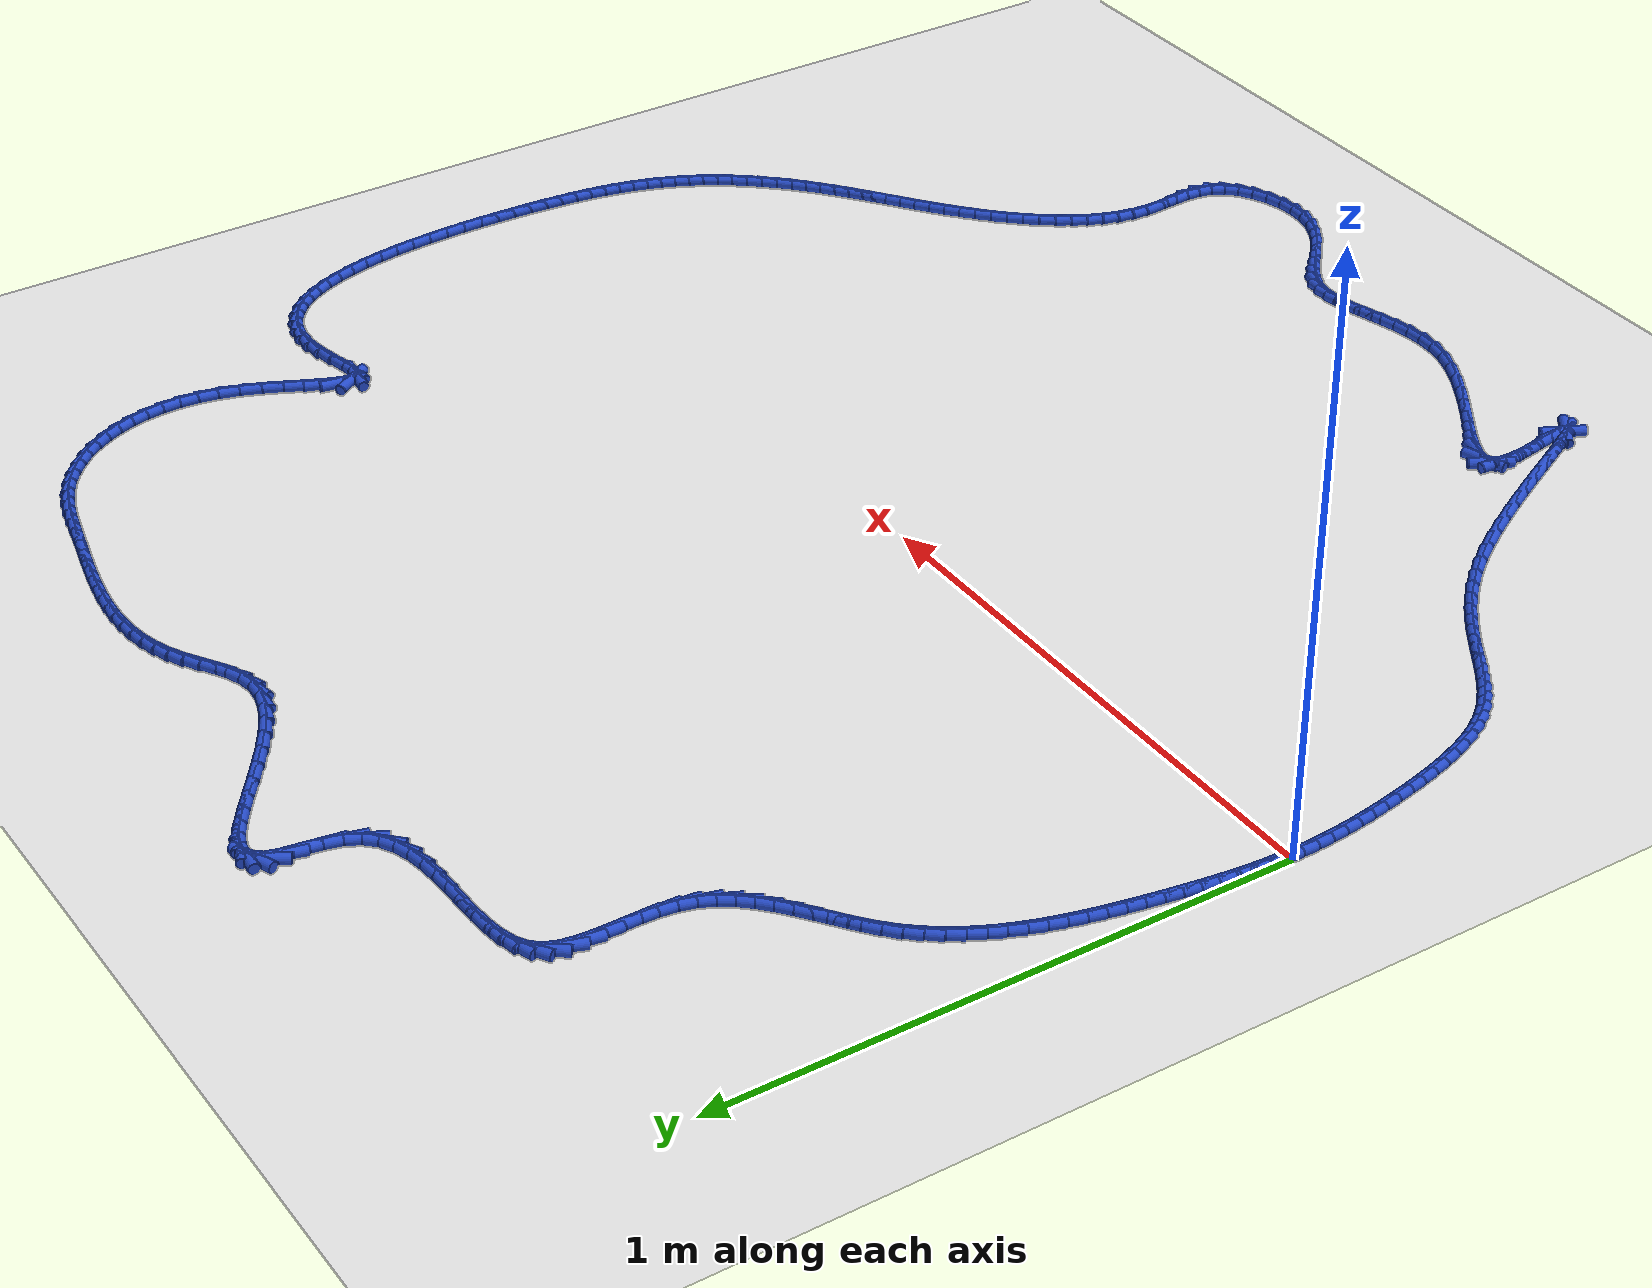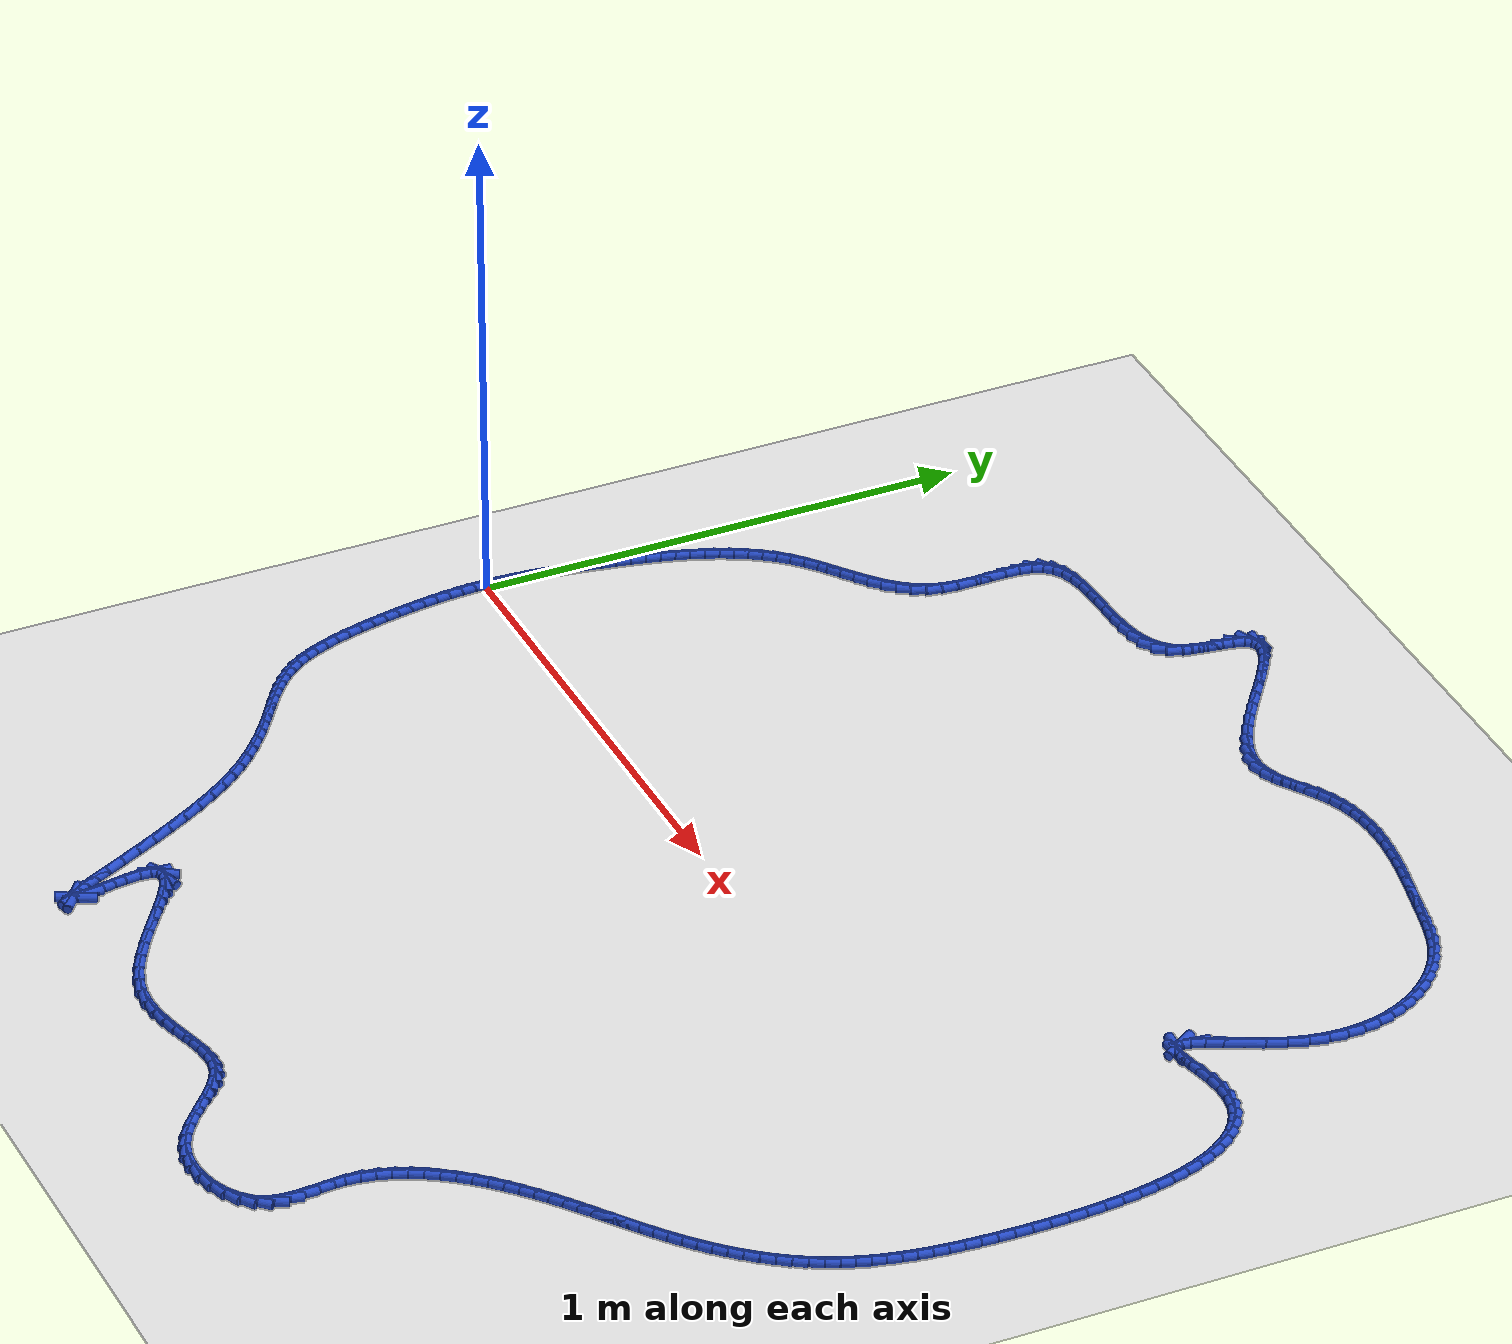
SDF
<sdf version="1.6">
 <world name="default">
  <light name="sun" type="directional">
   <pose>0 0 10 0 -0 0</pose>
   <diffuse>0.8 0.8 0.8 1</diffuse>
   <specular>0.2 0.2 0.2 1</specular>
   <attenuation>
    <range>1000</range>
    <constant>0.9</constant>
    <linear>0.01</linear>
    <quadratic>0.001</quadratic>
   </attenuation>
   <direction>-0.5 0.1 -0.9</direction>
  </light>
  <model name="ground_plane">
   <static>1</static>
   <link name="link">
    <collision name="collision">
     <geometry><plane><normal>0 0 1</normal><size>100 100</size></plane></geometry>
     <surface><friction><ode><mu>100</mu><mu2>50</mu2></ode></friction></surface>
    </collision>
    <visual name="visual">
     <cast_shadows>0</cast_shadows>
     <geometry><plane><normal>0 0 1</normal><size>100 100</size></plane></geometry>
     <material>
      <script><uri>file://media/materials/scripts/gazebo.material</uri><name>Gazebo/WhiteGlow</name></script>
     </material>
    </visual>
   </link>
  </model>
  <gravity>0 0 -9.8</gravity>
  <magnetic_field>6e-06 2.3e-05 -4.2e-05</magnetic_field>
  <atmosphere type="adiabatic"/>
  <physics name="default_physics" default="0" type="ode">
   <max_step_size>0.001</max_step_size>
   <real_time_factor>1</real_time_factor>
   <real_time_update_rate>1000</real_time_update_rate>
  </physics>
  <scene><ambient>0.4 0.4 0.4 1</ambient><background>0.7 0.7 0.7 1</background><shadows>1</shadows></scene>
  <spherical_coordinates>
   <surface_model>EARTH_WGS84</surface_model>
   <latitude_deg>0</latitude_deg>
   <longitude_deg>0</longitude_deg>
   <elevation>0</elevation>
   <heading_deg>0</heading_deg>
  </spherical_coordinates>
  <model name="line">
   <link name="link_0">
    <pose>-2.6020852139652106e-18 2.7755575615628914e-17 0.01 0 1.57 1.5460825741997606</pose>
    <collision name="collision">
     <geometry><cylinder><radius>0.01</radius><length>0.08</length></cylinder></geometry>
    </collision>
    <visual name="visual">
     <material>
      <script><name>Gazebo/Blue</name><uri>file://media/materials/scripts/gazebo.material</uri></script>
     </material>
     <geometry><cylinder><radius>0.01</radius><length>0.08</length></cylinder></geometry>
    </visual>
   </link>
   <link name="link_1">
    <pose>0.0006957124696851008 0.0281450913307681 0.01 0 1.57 1.5133960565667233</pose>
    <collision name="collision">
     <geometry><cylinder><radius>0.01</radius><length>0.08</length></cylinder></geometry>
    </collision>
    <visual name="visual">
     <material>
      <script><name>Gazebo/Blue</name><uri>file://media/materials/scripts/gazebo.material</uri></script>
     </material>
     <geometry><cylinder><radius>0.01</radius><length>0.08</length></cylinder></geometry>
    </visual>
   </link>
   <link name="link_2">
    <pose>0.00231621827940182 0.05634575431666636 0.01 0 1.57 1.4844393712283537</pose>
    <collision name="collision">
     <geometry><cylinder><radius>0.01</radius><length>0.08</length></cylinder></geometry>
    </collision>
    <visual name="visual">
     <material>
      <script><name>Gazebo/Blue</name><uri>file://media/materials/scripts/gazebo.material</uri></script>
     </material>
     <geometry><cylinder><radius>0.01</radius><length>0.08</length></cylinder></geometry>
    </visual>
   </link>
   <link name="link_3">
    <pose>0.004763729049343017 0.08461705688505244 0.01 0 1.57 1.4592352928734107</pose>
    <collision name="collision">
     <geometry><cylinder><radius>0.01</radius><length>0.08</length></cylinder></geometry>
    </collision>
    <visual name="visual">
     <material>
      <script><name>Gazebo/Blue</name><uri>file://media/materials/scripts/gazebo.material</uri></script>
     </material>
     <geometry><cylinder><radius>0.01</radius><length>0.08</length></cylinder></geometry>
    </visual>
   </link>
   <link name="link_4">
    <pose>0.007940456399701545 0.11297406696328394 0.01 0 1.57 1.4377689135698544</pose>
    <collision name="collision">
     <geometry><cylinder><radius>0.01</radius><length>0.08</length></cylinder></geometry>
    </collision>
    <visual name="visual">
     <material>
      <script><name>Gazebo/Blue</name><uri>file://media/materials/scripts/gazebo.material</uri></script>
     </material>
     <geometry><cylinder><radius>0.01</radius><length>0.08</length></cylinder></geometry>
    </visual>
   </link>
   <link name="link_5">
    <pose>0.011748611950670269 0.14143185247871848 0.01 0 1.57 1.4199987259306481</pose>
    <collision name="collision">
     <geometry><cylinder><radius>0.01</radius><length>0.08</length></cylinder></geometry>
    </collision>
    <visual name="visual">
     <material>
      <script><name>Gazebo/Blue</name><uri>file://media/materials/scripts/gazebo.material</uri></script>
     </material>
     <geometry><cylinder><radius>0.01</radius><length>0.08</length></cylinder></geometry>
    </visual>
   </link>
   <link name="link_6">
    <pose>0.01609040732244205 0.17000548135871377 0.01 0 1.57 1.4058660574432529</pose>
    <collision name="collision">
     <geometry><cylinder><radius>0.01</radius><length>0.08</length></cylinder></geometry>
    </collision>
    <visual name="visual">
     <material>
      <script><name>Gazebo/Blue</name><uri>file://media/materials/scripts/gazebo.material</uri></script>
     </material>
     <geometry><cylinder><radius>0.01</radius><length>0.08</length></cylinder></geometry>
    </visual>
   </link>
   <link name="link_7">
    <pose>0.02086805413520973 0.19871002153062717 0.01 0 1.57 1.3952951103471207</pose>
    <collision name="collision">
     <geometry><cylinder><radius>0.01</radius><length>0.08</length></cylinder></geometry>
    </collision>
    <visual name="visual">
     <material>
      <script><name>Gazebo/Blue</name><uri>file://media/materials/scripts/gazebo.material</uri></script>
     </material>
     <geometry><cylinder><radius>0.01</radius><length>0.08</length></cylinder></geometry>
    </visual>
   </link>
   <link name="link_8">
    <pose>0.02598396773254256 0.22756042493904283 0.01 0 1.57 1.3859469270723759</pose>
    <collision name="collision">
     <geometry><cylinder><radius>0.01</radius><length>0.08</length></cylinder></geometry>
    </collision>
    <visual name="visual">
     <material>
      <script><name>Gazebo/Blue</name><uri>file://media/materials/scripts/gazebo.material</uri></script>
     </material>
     <geometry><cylinder><radius>0.01</radius><length>0.08</length></cylinder></geometry>
    </visual>
   </link>
   <link name="link_9">
    <pose>0.03140205467062354 0.2565366356589112 0.01 0 1.57 1.3723373939159056</pose>
    <collision name="collision">
     <geometry><cylinder><radius>0.01</radius><length>0.08</length></cylinder></geometry>
    </collision>
    <visual name="visual">
     <material>
      <script><name>Gazebo/Blue</name><uri>file://media/materials/scripts/gazebo.material</uri></script>
     </material>
     <geometry><cylinder><radius>0.01</radius><length>0.08</length></cylinder></geometry>
    </visual>
   </link>
   <link name="link_10">
    <pose>0.03723372754716174 0.2855346203633341 0.01 0 1.57 1.353599764062397</pose>
    <collision name="collision">
     <geometry><cylinder><radius>0.01</radius><length>0.08</length></cylinder></geometry>
    </collision>
    <visual name="visual">
     <material>
      <script><name>Gazebo/Blue</name><uri>file://media/materials/scripts/gazebo.material</uri></script>
     </material>
     <geometry><cylinder><radius>0.01</radius><length>0.08</length></cylinder></geometry>
    </visual>
   </link>
   <link name="link_11">
    <pose>0.043612059992815574 0.31443801377446645 0.01 0 1.57 1.3295948969485154</pose>
    <collision name="collision">
     <geometry><cylinder><radius>0.01</radius><length>0.08</length></cylinder></geometry>
    </collision>
    <visual name="visual">
     <material>
      <script><name>Gazebo/Blue</name><uri>file://media/materials/scripts/gazebo.material</uri></script>
     </material>
     <geometry><cylinder><radius>0.01</radius><length>0.08</length></cylinder></geometry>
    </visual>
   </link>
   <link name="link_12">
    <pose>0.05067012563824344 0.34313045061446323 0.01 0 1.57 1.3001220045204205</pose>
    <collision name="collision">
     <geometry><cylinder><radius>0.01</radius><length>0.08</length></cylinder></geometry>
    </collision>
    <visual name="visual">
     <material>
      <script><name>Gazebo/Blue</name><uri>file://media/materials/scripts/gazebo.material</uri></script>
     </material>
     <geometry><cylinder><radius>0.01</radius><length>0.08</length></cylinder></geometry>
    </visual>
   </link>
   <link name="link_13">
    <pose>0.05854099811410375 0.37149556560547925 0.01 0 1.57 1.264935044091737</pose>
    <collision name="collision">
     <geometry><cylinder><radius>0.01</radius><length>0.08</length></cylinder></geometry>
    </collision>
    <visual name="visual">
     <material>
      <script><name>Gazebo/Blue</name><uri>file://media/materials/scripts/gazebo.material</uri></script>
     </material>
     <geometry><cylinder><radius>0.01</radius><length>0.08</length></cylinder></geometry>
    </visual>
   </link>
   <link name="link_14">
    <pose>0.06735775105105489 0.3994169934696695 0.01 0 1.57 1.223765772698861</pose>
    <collision name="collision">
     <geometry><cylinder><radius>0.01</radius><length>0.08</length></cylinder></geometry>
    </collision>
    <visual name="visual">
     <material>
      <script><name>Gazebo/Blue</name><uri>file://media/materials/scripts/gazebo.material</uri></script>
     </material>
     <geometry><cylinder><radius>0.01</radius><length>0.08</length></cylinder></geometry>
    </visual>
   </link>
   <link name="link_15">
    <pose>0.07725345807975528 0.42677836892918897 0.01 0 1.57 1.17635642199306</pose>
    <collision name="collision">
     <geometry><cylinder><radius>0.01</radius><length>0.08</length></cylinder></geometry>
    </collision>
    <visual name="visual">
     <material>
      <script><name>Gazebo/Blue</name><uri>file://media/materials/scripts/gazebo.material</uri></script>
     </material>
     <geometry><cylinder><radius>0.01</radius><length>0.08</length></cylinder></geometry>
    </visual>
   </link>
   <link name="link_16">
    <pose>0.08836119283086336 0.45346332670619266 0.01 0 1.57 1.1225046997633035</pose>
    <collision name="collision">
     <geometry><cylinder><radius>0.01</radius><length>0.08</length></cylinder></geometry>
    </collision>
    <visual name="visual">
     <material>
      <script><name>Gazebo/Blue</name><uri>file://media/materials/scripts/gazebo.material</uri></script>
     </material>
     <geometry><cylinder><radius>0.01</radius><length>0.08</length></cylinder></geometry>
    </visual>
   </link>
   <link name="link_17">
    <pose>0.10081402893503746 0.47935550152283524 0.01 0 1.57 1.0621223965960767</pose>
    <collision name="collision">
     <geometry><cylinder><radius>0.01</radius><length>0.08</length></cylinder></geometry>
    </collision>
    <visual name="visual">
     <material>
      <script><name>Gazebo/Blue</name><uri>file://media/materials/scripts/gazebo.material</uri></script>
     </material>
     <geometry><cylinder><radius>0.01</radius><length>0.08</length></cylinder></geometry>
    </visual>
   </link>
   <link name="link_18">
    <pose>0.11474504002293606 0.5043385281012721 0.01 0 1.57 0.9953055394524062</pose>
    <collision name="collision">
     <geometry><cylinder><radius>0.01</radius><length>0.08</length></cylinder></geometry>
    </collision>
    <visual name="visual">
     <material>
      <script><name>Gazebo/Blue</name><uri>file://media/materials/scripts/gazebo.material</uri></script>
     </material>
     <geometry><cylinder><radius>0.01</radius><length>0.08</length></cylinder></geometry>
    </visual>
   </link>
   <link name="link_19">
    <pose>0.13028729972521755 0.5282960411636578 0.01 0 1.57 0.922408352016802</pose>
    <collision name="collision">
     <geometry><cylinder><radius>0.01</radius><length>0.08</length></cylinder></geometry>
    </collision>
    <visual name="visual">
     <material>
      <script><name>Gazebo/Blue</name><uri>file://media/materials/scripts/gazebo.material</uri></script>
     </material>
     <geometry><cylinder><radius>0.01</radius><length>0.08</length></cylinder></geometry>
    </visual>
   </link>
   <link name="link_20">
    <pose>0.14757388167254032 0.5511116754321475 0.01 0 1.57 0.8441059657487131</pose>
    <collision name="collision">
     <geometry><cylinder><radius>0.01</radius><length>0.08</length></cylinder></geometry>
    </collision>
    <visual name="visual">
     <material>
      <script><name>Gazebo/Blue</name><uri>file://media/materials/scripts/gazebo.material</uri></script>
     </material>
     <geometry><cylinder><radius>0.01</radius><length>0.08</length></cylinder></geometry>
    </visual>
   </link>
   <link name="link_21">
    <pose>0.1667378594955628 0.5726690656288959 0.01 0 1.57 0.762438806571426</pose>
    <collision name="collision">
     <geometry><cylinder><radius>0.01</radius><length>0.08</length></cylinder></geometry>
    </collision>
    <visual name="visual">
     <material>
      <script><name>Gazebo/Blue</name><uri>file://media/materials/scripts/gazebo.material</uri></script>
     </material>
     <geometry><cylinder><radius>0.01</radius><length>0.08</length></cylinder></geometry>
    </visual>
   </link>
   <link name="link_22">
    <pose>0.18788723665252804 0.5928689240845005 0.01 0 1.57 0.6950614117786142</pose>
    <collision name="collision">
     <geometry><cylinder><radius>0.01</radius><length>0.08</length></cylinder></geometry>
    </collision>
    <visual name="visual">
     <material>
      <script><name>Gazebo/Blue</name><uri>file://media/materials/scripts/gazebo.material</uri></script>
     </material>
     <geometry><cylinder><radius>0.01</radius><length>0.08</length></cylinder></geometry>
    </visual>
   </link>
   <link name="link_23">
    <pose>0.2107084700605852 0.6118991173880096 0.01 0 1.57 0.6545456691266348</pose>
    <collision name="collision">
     <geometry><cylinder><radius>0.01</radius><length>0.08</length></cylinder></geometry>
    </collision>
    <visual name="visual">
     <material>
      <script><name>Gazebo/Blue</name><uri>file://media/materials/scripts/gazebo.material</uri></script>
     </material>
     <geometry><cylinder><radius>0.01</radius><length>0.08</length></cylinder></geometry>
    </visual>
   </link>
   <link name="link_24">
    <pose>0.23453799647686543 0.6301859431667889 0.01 0 1.57 0.639629527414747</pose>
    <collision name="collision">
     <geometry><cylinder><radius>0.01</radius><length>0.08</length></cylinder></geometry>
    </collision>
    <visual name="visual">
     <material>
      <script><name>Gazebo/Blue</name><uri>file://media/materials/scripts/gazebo.material</uri></script>
     </material>
     <geometry><cylinder><radius>0.01</radius><length>0.08</length></cylinder></geometry>
    </visual>
   </link>
   <link name="link_25">
    <pose>0.2587016429815712 0.648162926278448 0.01 0 1.57 0.6497303249937508</pose>
    <collision name="collision">
     <geometry><cylinder><radius>0.01</radius><length>0.08</length></cylinder></geometry>
    </collision>
    <visual name="visual">
     <material>
      <script><name>Gazebo/Blue</name><uri>file://media/materials/scripts/gazebo.material</uri></script>
     </material>
     <geometry><cylinder><radius>0.01</radius><length>0.08</length></cylinder></geometry>
    </visual>
   </link>
   <link name="link_26">
    <pose>0.28252523665490514 0.6662635915805967 0.01 0 1.57 0.6856155836763922</pose>
    <collision name="collision">
     <geometry><cylinder><radius>0.01</radius><length>0.08</length></cylinder></geometry>
    </collision>
    <visual name="visual">
     <material>
      <script><name>Gazebo/Blue</name><uri>file://media/materials/scripts/gazebo.material</uri></script>
     </material>
     <geometry><cylinder><radius>0.01</radius><length>0.08</length></cylinder></geometry>
    </visual>
   </link>
   <link name="link_27">
    <pose>0.3053346045770696 0.6849214639308446 0.01 0 1.57 0.7492995422526305</pose>
    <collision name="collision">
     <geometry><cylinder><radius>0.01</radius><length>0.08</length></cylinder></geometry>
    </collision>
    <visual name="visual">
     <material>
      <script><name>Gazebo/Blue</name><uri>file://media/materials/scripts/gazebo.material</uri></script>
     </material>
     <geometry><cylinder><radius>0.01</radius><length>0.08</length></cylinder></geometry>
    </visual>
   </link>
   <link name="link_28">
    <pose>0.32645557382826734 0.7045700681868013 0.01 0 1.57 0.8434396076398463</pose>
    <collision name="collision">
     <geometry><cylinder><radius>0.01</radius><length>0.08</length></cylinder></geometry>
    </collision>
    <visual name="visual">
     <material>
      <script><name>Gazebo/Blue</name><uri>file://media/materials/scripts/gazebo.material</uri></script>
     </material>
     <geometry><cylinder><radius>0.01</radius><length>0.08</length></cylinder></geometry>
    </visual>
   </link>
   <link name="link_29">
    <pose>0.3452139714887008 0.7256429292060768 0.01 0 1.57 0.9697883097614433</pose>
    <collision name="collision">
     <geometry><cylinder><radius>0.01</radius><length>0.08</length></cylinder></geometry>
    </collision>
    <visual name="visual">
     <material>
      <script><name>Gazebo/Blue</name><uri>file://media/materials/scripts/gazebo.material</uri></script>
     </material>
     <geometry><cylinder><radius>0.01</radius><length>0.08</length></cylinder></geometry>
    </visual>
   </link>
   <link name="link_30">
    <pose>0.36093562463857254 0.7485735718462805 0.01 0 1.57 1.1263679460517388</pose>
    <collision name="collision">
     <geometry><cylinder><radius>0.01</radius><length>0.08</length></cylinder></geometry>
    </collision>
    <visual name="visual">
     <material>
      <script><name>Gazebo/Blue</name><uri>file://media/materials/scripts/gazebo.material</uri></script>
     </material>
     <geometry><cylinder><radius>0.01</radius><length>0.08</length></cylinder></geometry>
    </visual>
   </link>
   <link name="link_31">
    <pose>0.37294636035808515 0.7737955209650219 0.01 0 1.57 1.3030096611344328</pose>
    <collision name="collision">
     <geometry><cylinder><radius>0.01</radius><length>0.08</length></cylinder></geometry>
    </collision>
    <visual name="visual">
     <material>
      <script><name>Gazebo/Blue</name><uri>file://media/materials/scripts/gazebo.material</uri></script>
     </material>
     <geometry><cylinder><radius>0.01</radius><length>0.08</length></cylinder></geometry>
    </visual>
   </link>
   <link name="link_32">
    <pose>0.3806072520532231 0.8017165906903553 0.01 0 1.57 1.4518044396515537</pose>
    <collision name="collision">
     <geometry><cylinder><radius>0.01</radius><length>0.08</length></cylinder></geometry>
    </collision>
    <visual name="visual">
     <material>
      <script><name>Gazebo/Blue</name><uri>file://media/materials/scripts/gazebo.material</uri></script>
     </material>
     <geometry><cylinder><radius>0.01</radius><length>0.08</length></cylinder></geometry>
    </visual>
   </link>
   <link name="link_33">
    <pose>0.38423363486674517 0.8320485008796518 0.01 0 1.57 1.540869643582424</pose>
    <collision name="collision">
     <geometry><cylinder><radius>0.01</radius><length>0.08</length></cylinder></geometry>
    </collision>
    <visual name="visual">
     <material>
      <script><name>Gazebo/Blue</name><uri>file://media/materials/scripts/gazebo.material</uri></script>
     </material>
     <geometry><cylinder><radius>0.01</radius><length>0.08</length></cylinder></geometry>
    </visual>
   </link>
   <link name="link_34">
    <pose>0.3851824345853442 0.8637431743118724 0.01 0 1.57 -1.5608155906507495</pose>
    <collision name="collision">
     <geometry><cylinder><radius>0.01</radius><length>0.08</length></cylinder></geometry>
    </collision>
    <visual name="visual">
     <material>
      <script><name>Gazebo/Blue</name><uri>file://media/materials/scripts/gazebo.material</uri></script>
     </material>
     <geometry><cylinder><radius>0.01</radius><length>0.08</length></cylinder></geometry>
    </visual>
   </link>
   <link name="link_35">
    <pose>0.38486333109650434 0.8957140518423091 0.01 0 1.57 -1.5651056361236841</pose>
    <collision name="collision">
     <geometry><cylinder><radius>0.01</radius><length>0.08</length></cylinder></geometry>
    </collision>
    <visual name="visual">
     <material>
      <script><name>Gazebo/Blue</name><uri>file://media/materials/scripts/gazebo.material</uri></script>
     </material>
     <geometry><cylinder><radius>0.01</radius><length>0.08</length></cylinder></geometry>
    </visual>
   </link>
   <link name="link_36">
    <pose>0.38468600428770927 0.9268745743262523 0.01 0 1.57 1.523873844978217</pose>
    <collision name="collision">
     <geometry><cylinder><radius>0.01</radius><length>0.08</length></cylinder></geometry>
    </collision>
    <visual name="visual">
     <material>
      <script><name>Gazebo/Blue</name><uri>file://media/materials/scripts/gazebo.material</uri></script>
     </material>
     <geometry><cylinder><radius>0.01</radius><length>0.08</length></cylinder></geometry>
    </visual>
   </link>
   <link name="link_37">
    <pose>0.3860601340464434 0.956138182618994 0.01 0 1.57 1.407305123349168</pose>
    <collision name="collision">
     <geometry><cylinder><radius>0.01</radius><length>0.08</length></cylinder></geometry>
    </collision>
    <visual name="visual">
     <material>
      <script><name>Gazebo/Blue</name><uri>file://media/materials/scripts/gazebo.material</uri></script>
     </material>
     <geometry><cylinder><radius>0.01</radius><length>0.08</length></cylinder></geometry>
    </visual>
   </link>
   <link name="link_38">
    <pose>0.3903954002601905 0.9824183175758252 0.01 0 1.57 1.1972163033865266</pose>
    <collision name="collision">
     <geometry><cylinder><radius>0.01</radius><length>0.08</length></cylinder></geometry>
    </collision>
    <visual name="visual">
     <material>
      <script><name>Gazebo/Blue</name><uri>file://media/materials/scripts/gazebo.material</uri></script>
     </material>
     <geometry><cylinder><radius>0.01</radius><length>0.08</length></cylinder></geometry>
    </visual>
   </link>
   <link name="link_39">
    <pose>0.39910148281643476 1.0046284200520372 0.01 0 1.57 0.8710041887118876</pose>
    <collision name="collision">
     <geometry><cylinder><radius>0.01</radius><length>0.08</length></cylinder></geometry>
    </collision>
    <visual name="visual">
     <material>
      <script><name>Gazebo/Blue</name><uri>file://media/materials/scripts/gazebo.material</uri></script>
     </material>
     <geometry><cylinder><radius>0.01</radius><length>0.08</length></cylinder></geometry>
    </visual>
   </link>
   <link name="link_40">
    <pose>0.41351301395609796 1.021745612515842 0.01 0 1.57 0.538513415247076</pose>
    <collision name="collision">
     <geometry><cylinder><radius>0.01</radius><length>0.08</length></cylinder></geometry>
    </collision>
    <visual name="visual">
     <material>
      <script><name>Gazebo/Blue</name><uri>file://media/materials/scripts/gazebo.material</uri></script>
     </material>
     <geometry><cylinder><radius>0.01</radius><length>0.08</length></cylinder></geometry>
    </visual>
   </link>
   <link name="link_41">
    <pose>0.4337100839562882 1.0338115578893134 0.01 0 1.57 0.3071287312632298</pose>
    <collision name="collision">
     <geometry><cylinder><radius>0.01</radius><length>0.08</length></cylinder></geometry>
    </collision>
    <visual name="visual">
     <material>
      <script><name>Gazebo/Blue</name><uri>file://media/materials/scripts/gazebo.material</uri></script>
     </material>
     <geometry><cylinder><radius>0.01</radius><length>0.08</length></cylinder></geometry>
    </visual>
   </link>
   <link name="link_42">
    <pose>0.458734962007678 1.0417485612430142 0.01 0 1.57 0.16333557807781535</pose>
    <collision name="collision">
     <geometry><cylinder><radius>0.01</radius><length>0.08</length></cylinder></geometry>
    </collision>
    <visual name="visual">
     <material>
      <script><name>Gazebo/Blue</name><uri>file://media/materials/scripts/gazebo.material</uri></script>
     </material>
     <geometry><cylinder><radius>0.01</radius><length>0.08</length></cylinder></geometry>
    </visual>
   </link>
   <link name="link_43">
    <pose>0.48759870310117037 1.0465054144286154 0.01 0 1.57 0.07946659525231903</pose>
    <collision name="collision">
     <geometry><cylinder><radius>0.01</radius><length>0.08</length></cylinder></geometry>
    </collision>
    <visual name="visual">
     <material>
      <script><name>Gazebo/Blue</name><uri>file://media/materials/scripts/gazebo.material</uri></script>
     </material>
     <geometry><cylinder><radius>0.01</radius><length>0.08</length></cylinder></geometry>
    </visual>
   </link>
   <link name="link_44">
    <pose>0.5193123622276699 1.0490309092977899 0.01 0 1.57 0.037002968978884214</pose>
    <collision name="collision">
     <geometry><cylinder><radius>0.01</radius><length>0.08</length></cylinder></geometry>
    </collision>
    <visual name="visual">
     <material>
      <script><name>Gazebo/Blue</name><uri>file://media/materials/scripts/gazebo.material</uri></script>
     </material>
     <geometry><cylinder><radius>0.01</radius><length>0.08</length></cylinder></geometry>
    </visual>
   </link>
   <link name="link_45">
    <pose>0.5528869943780791 1.050273837702209 0.01 0 1.57 0.02638696381926445</pose>
    <collision name="collision">
     <geometry><cylinder><radius>0.01</radius><length>0.08</length></cylinder></geometry>
    </collision>
    <visual name="visual">
     <material>
      <script><name>Gazebo/Blue</name><uri>file://media/materials/scripts/gazebo.material</uri></script>
     </material>
     <geometry><cylinder><radius>0.01</radius><length>0.08</length></cylinder></geometry>
    </visual>
   </link>
   <link name="link_46">
    <pose>0.5873336545433022 1.0511829914935453 0.01 0 1.57 0.04436883588901307</pose>
    <collision name="collision">
     <geometry><cylinder><radius>0.01</radius><length>0.08</length></cylinder></geometry>
    </collision>
    <visual name="visual">
     <material>
      <script><name>Gazebo/Blue</name><uri>file://media/materials/scripts/gazebo.material</uri></script>
     </material>
     <geometry><cylinder><radius>0.01</radius><length>0.08</length></cylinder></geometry>
    </visual>
   </link>
   <link name="link_47">
    <pose>0.6216633977142424 1.052707162523471 0.01 0 1.57 0.0926783318782825</pose>
    <collision name="collision">
     <geometry><cylinder><radius>0.01</radius><length>0.08</length></cylinder></geometry>
    </collision>
    <visual name="visual">
     <material>
      <script><name>Gazebo/Blue</name><uri>file://media/materials/scripts/gazebo.material</uri></script>
     </material>
     <geometry><cylinder><radius>0.01</radius><length>0.08</length></cylinder></geometry>
    </visual>
   </link>
   <link name="link_48">
    <pose>0.6548872788818034 1.0557951426436576 0.01 0 1.57 0.1780104080934397</pose>
    <collision name="collision">
     <geometry><cylinder><radius>0.01</radius><length>0.08</length></cylinder></geometry>
    </collision>
    <visual name="visual">
     <material>
      <script><name>Gazebo/Blue</name><uri>file://media/materials/scripts/gazebo.material</uri></script>
     </material>
     <geometry><cylinder><radius>0.01</radius><length>0.08</length></cylinder></geometry>
    </visual>
   </link>
   <link name="link_49">
    <pose>0.6860163530368887 1.0613957237057778 0.01 0 1.57 0.3125295758366332</pose>
    <collision name="collision">
     <geometry><cylinder><radius>0.01</radius><length>0.08</length></cylinder></geometry>
    </collision>
    <visual name="visual">
     <material>
      <script><name>Gazebo/Blue</name><uri>file://media/materials/scripts/gazebo.material</uri></script>
     </material>
     <geometry><cylinder><radius>0.01</radius><length>0.08</length></cylinder></geometry>
    </visual>
   </link>
   <link name="link_50">
    <pose>0.7140616751704021 1.0704576975615034 0.01 0 1.57 0.5119950756194789</pose>
    <collision name="collision">
     <geometry><cylinder><radius>0.01</radius><length>0.08</length></cylinder></geometry>
    </collision>
    <visual name="visual">
     <material>
      <script><name>Gazebo/Blue</name><uri>file://media/materials/scripts/gazebo.material</uri></script>
     </material>
     <geometry><cylinder><radius>0.01</radius><length>0.08</length></cylinder></geometry>
    </visual>
   </link>
   <link name="link_51">
    <pose>0.7380343002732463 1.083929856062506 0.01 0 1.57 0.7832825442933845</pose>
    <collision name="collision">
     <geometry><cylinder><radius>0.01</radius><length>0.08</length></cylinder></geometry>
    </collision>
    <visual name="visual">
     <material>
      <script><name>Gazebo/Blue</name><uri>file://media/materials/scripts/gazebo.material</uri></script>
     </material>
     <geometry><cylinder><radius>0.01</radius><length>0.08</length></cylinder></geometry>
    </visual>
   </link>
   <link name="link_52">
    <pose>0.7569452833363259 1.1027609910604586 0.01 0 1.57 1.093611160135322</pose>
    <collision name="collision">
     <geometry><cylinder><radius>0.01</radius><length>0.08</length></cylinder></geometry>
    </collision>
    <visual name="visual">
     <material>
      <script><name>Gazebo/Blue</name><uri>file://media/materials/scripts/gazebo.material</uri></script>
     </material>
     <geometry><cylinder><radius>0.01</radius><length>0.08</length></cylinder></geometry>
    </visual>
   </link>
   <link name="link_53">
    <pose>0.7698869036961941 1.1277912836832347 0.01 0 1.57 1.3171710842812099</pose>
    <collision name="collision">
     <geometry><cylinder><radius>0.01</radius><length>0.08</length></cylinder></geometry>
    </collision>
    <visual name="visual">
     <material>
      <script><name>Gazebo/Blue</name><uri>file://media/materials/scripts/gazebo.material</uri></script>
     </material>
     <geometry><cylinder><radius>0.01</radius><length>0.08</length></cylinder></geometry>
    </visual>
   </link>
   <link name="link_54">
    <pose>0.7776209293300023 1.1576285256417682 0.01 0 1.57 1.4162436817964565</pose>
    <collision name="collision">
     <geometry><cylinder><radius>0.01</radius><length>0.08</length></cylinder></geometry>
    </collision>
    <visual name="visual">
     <material>
      <script><name>Gazebo/Blue</name><uri>file://media/materials/scripts/gazebo.material</uri></script>
     </material>
     <geometry><cylinder><radius>0.01</radius><length>0.08</length></cylinder></geometry>
    </visual>
   </link>
   <link name="link_55">
    <pose>0.7824751785154104 1.1887864338313676 0.01 0 1.57 1.421023795153077</pose>
    <collision name="collision">
     <geometry><cylinder><radius>0.01</radius><length>0.08</length></cylinder></geometry>
    </collision>
    <visual name="visual">
     <material>
      <script><name>Gazebo/Blue</name><uri>file://media/materials/scripts/gazebo.material</uri></script>
     </material>
     <geometry><cylinder><radius>0.01</radius><length>0.08</length></cylinder></geometry>
    </visual>
   </link>
   <link name="link_56">
    <pose>0.7868379796734247 1.217697812824643 0.01 0 1.57 1.3061439129063204</pose>
    <collision name="collision">
     <geometry><cylinder><radius>0.01</radius><length>0.08</length></cylinder></geometry>
    </collision>
    <visual name="visual">
     <material>
      <script><name>Gazebo/Blue</name><uri>file://media/materials/scripts/gazebo.material</uri></script>
     </material>
     <geometry><cylinder><radius>0.01</radius><length>0.08</length></cylinder></geometry>
    </visual>
   </link>
   <link name="link_57">
    <pose>0.7930976612250524 1.2407954671942054 0.01 0 1.57 0.9519212778368862</pose>
    <collision name="collision">
     <geometry><cylinder><radius>0.01</radius><length>0.08</length></cylinder></geometry>
    </collision>
    <visual name="visual">
     <material>
      <script><name>Gazebo/Blue</name><uri>file://media/materials/scripts/gazebo.material</uri></script>
     </material>
     <geometry><cylinder><radius>0.01</radius><length>0.08</length></cylinder></geometry>
    </visual>
   </link>
   <link name="link_58">
    <pose>0.8032892506888681 1.255105235192542 0.01 0 1.57 0.37667151292999956</pose>
    <collision name="collision">
     <geometry><cylinder><radius>0.01</radius><length>0.08</length></cylinder></geometry>
    </collision>
    <visual name="visual">
     <material>
      <script><name>Gazebo/Blue</name><uri>file://media/materials/scripts/gazebo.material</uri></script>
     </material>
     <geometry><cylinder><radius>0.01</radius><length>0.08</length></cylinder></geometry>
    </visual>
   </link>
   <link name="link_59">
    <pose>0.8175944889934978 1.2607637916387517 0.01 0 1.57 -0.10186619009313393</pose>
    <collision name="collision">
     <geometry><cylinder><radius>0.01</radius><length>0.08</length></cylinder></geometry>
    </collision>
    <visual name="visual">
     <material>
      <script><name>Gazebo/Blue</name><uri>file://media/materials/scripts/gazebo.material</uri></script>
     </material>
     <geometry><cylinder><radius>0.01</radius><length>0.08</length></cylinder></geometry>
    </visual>
   </link>
   <link name="link_60">
    <pose>0.8355895184719175 1.2589243396461833 0.01 0 1.57 -0.3674410583578735</pose>
    <collision name="collision">
     <geometry><cylinder><radius>0.01</radius><length>0.08</length></cylinder></geometry>
    </collision>
    <visual name="visual">
     <material>
      <script><name>Gazebo/Blue</name><uri>file://media/materials/scripts/gazebo.material</uri></script>
     </material>
     <geometry><cylinder><radius>0.01</radius><length>0.08</length></cylinder></geometry>
    </visual>
   </link>
   <link name="link_61">
    <pose>0.8568501403320983 1.250740654923999 0.01 0 1.57 -0.506595307896519</pose>
    <collision name="collision">
     <geometry><cylinder><radius>0.01</radius><length>0.08</length></cylinder></geometry>
    </collision>
    <visual name="visual">
     <material>
      <script><name>Gazebo/Blue</name><uri>file://media/materials/scripts/gazebo.material</uri></script>
     </material>
     <geometry><cylinder><radius>0.01</radius><length>0.08</length></cylinder></geometry>
    </visual>
   </link>
   <link name="link_62">
    <pose>0.8809521557820098 1.2373665131813592 0.01 0 1.57 -0.5809564146101333</pose>
    <collision name="collision">
     <geometry><cylinder><radius>0.01</radius><length>0.08</length></cylinder></geometry>
    </collision>
    <visual name="visual">
     <material>
      <script><name>Gazebo/Blue</name><uri>file://media/materials/scripts/gazebo.material</uri></script>
     </material>
     <geometry><cylinder><radius>0.01</radius><length>0.08</length></cylinder></geometry>
    </visual>
   </link>
   <link name="link_63">
    <pose>0.9074713660296231 1.2199556901274262 0.01 0 1.57 -0.6185722783904792</pose>
    <collision name="collision">
     <geometry><cylinder><radius>0.01</radius><length>0.08</length></cylinder></geometry>
    </collision>
    <visual name="visual">
     <material>
      <script><name>Gazebo/Blue</name><uri>file://media/materials/scripts/gazebo.material</uri></script>
     </material>
     <geometry><cylinder><radius>0.01</radius><length>0.08</length></cylinder></geometry>
    </visual>
   </link>
   <link name="link_64">
    <pose>0.9359835722829082 1.1996619614713615 0.01 0 1.57 -0.6319583717431225</pose>
    <collision name="collision">
     <geometry><cylinder><radius>0.01</radius><length>0.08</length></cylinder></geometry>
    </collision>
    <visual name="visual">
     <material>
      <script><name>Gazebo/Blue</name><uri>file://media/materials/scripts/gazebo.material</uri></script>
     </material>
     <geometry><cylinder><radius>0.01</radius><length>0.08</length></cylinder></geometry>
    </visual>
   </link>
   <link name="link_65">
    <pose>0.966064575749836 1.1776391029223265 0.01 0 1.57 -0.6264606977421062</pose>
    <collision name="collision">
     <geometry><cylinder><radius>0.01</radius><length>0.08</length></cylinder></geometry>
    </collision>
    <visual name="visual">
     <material>
      <script><name>Gazebo/Blue</name><uri>file://media/materials/scripts/gazebo.material</uri></script>
     </material>
     <geometry><cylinder><radius>0.01</radius><length>0.08</length></cylinder></geometry>
    </visual>
   </link>
   <link name="link_66">
    <pose>0.9972901776383769 1.1550408901894822 0.01 0 1.57 -0.6034961304598243</pose>
    <collision name="collision">
     <geometry><cylinder><radius>0.01</radius><length>0.08</length></cylinder></geometry>
    </collision>
    <visual name="visual">
     <material>
      <script><name>Gazebo/Blue</name><uri>file://media/materials/scripts/gazebo.material</uri></script>
     </material>
     <geometry><cylinder><radius>0.01</radius><length>0.08</length></cylinder></geometry>
    </visual>
   </link>
   <link name="link_67">
    <pose>1.029236179156501 1.1330210989819909 0.01 0 1.57 -0.5616316210973511</pose>
    <collision name="collision">
     <geometry><cylinder><radius>0.01</radius><length>0.08</length></cylinder></geometry>
    </collision>
    <visual name="visual">
     <material>
      <script><name>Gazebo/Blue</name><uri>file://media/materials/scripts/gazebo.material</uri></script>
     </material>
     <geometry><cylinder><radius>0.01</radius><length>0.08</length></cylinder></geometry>
    </visual>
   </link>
   <link name="link_68">
    <pose>1.0614783815121795 1.1127335050090132 0.01 0 1.57 -0.49657747092633964</pose>
    <collision name="collision">
     <geometry><cylinder><radius>0.01</radius><length>0.08</length></cylinder></geometry>
    </collision>
    <visual name="visual">
     <material>
      <script><name>Gazebo/Blue</name><uri>file://media/materials/scripts/gazebo.material</uri></script>
     </material>
     <geometry><cylinder><radius>0.01</radius><length>0.08</length></cylinder></geometry>
    </visual>
   </link>
   <link name="link_69">
    <pose>1.0935925859133824 1.0953318839797113 0.01 0 1.57 -0.40047484395990823</pose>
    <collision name="collision">
     <geometry><cylinder><radius>0.01</radius><length>0.08</length></cylinder></geometry>
    </collision>
    <visual name="visual">
     <material>
      <script><name>Gazebo/Blue</name><uri>file://media/materials/scripts/gazebo.material</uri></script>
     </material>
     <geometry><cylinder><radius>0.01</radius><length>0.08</length></cylinder></geometry>
    </visual>
   </link>
   <link name="link_70">
    <pose>1.1251545935680807 1.0819700116032467 0.01 0 1.57 -0.2609742890456194</pose>
    <collision name="collision">
     <geometry><cylinder><radius>0.01</radius><length>0.08</length></cylinder></geometry>
    </collision>
    <visual name="visual">
     <material>
      <script><name>Gazebo/Blue</name><uri>file://media/materials/scripts/gazebo.material</uri></script>
     </material>
     <geometry><cylinder><radius>0.01</radius><length>0.08</length></cylinder></geometry>
    </visual>
   </link>
   <link name="link_71">
    <pose>1.155740205684244 1.0738016635887804 0.01 0 1.57 -0.0623158825441884</pose>
    <collision name="collision">
     <geometry><cylinder><radius>0.01</radius><length>0.08</length></cylinder></geometry>
    </collision>
    <visual name="visual">
     <material>
      <script><name>Gazebo/Blue</name><uri>file://media/materials/scripts/gazebo.material</uri></script>
     </material>
     <geometry><cylinder><radius>0.01</radius><length>0.08</length></cylinder></geometry>
    </visual>
   </link>
   <link name="link_72">
    <pose>1.1849252234740182 1.0719806156311802 0.01 0 1.57 0.1851801011356724</pose>
    <collision name="collision">
     <geometry><cylinder><radius>0.01</radius><length>0.08</length></cylinder></geometry>
    </collision>
    <visual name="visual">
     <material>
      <script><name>Gazebo/Blue</name><uri>file://media/materials/scripts/gazebo.material</uri></script>
     </material>
     <geometry><cylinder><radius>0.01</radius><length>0.08</length></cylinder></geometry>
    </visual>
   </link>
   <link name="link_73">
    <pose>1.2124390527014814 1.0771346782395015 0.01 0 1.57 0.3870645522478079</pose>
    <collision name="collision">
     <geometry><cylinder><radius>0.01</radius><length>0.08</length></cylinder></geometry>
    </collision>
    <visual name="visual">
     <material>
      <script><name>Gazebo/Blue</name><uri>file://media/materials/scripts/gazebo.material</uri></script>
     </material>
     <geometry><cylinder><radius>0.01</radius><length>0.08</length></cylinder></geometry>
    </visual>
   </link>
   <link name="link_74">
    <pose>1.2386199839189125 1.087806748443775 0.01 0 1.57 0.5113178885886072</pose>
    <collision name="collision">
     <geometry><cylinder><radius>0.01</radius><length>0.08</length></cylinder></geometry>
    </collision>
    <visual name="visual">
     <material>
      <script><name>Gazebo/Blue</name><uri>file://media/materials/scripts/gazebo.material</uri></script>
     </material>
     <geometry><cylinder><radius>0.01</radius><length>0.08</length></cylinder></geometry>
    </visual>
   </link>
   <link name="link_75">
    <pose>1.2639571579565916 1.1020231891381715 0.01 0 1.57 0.5635656389518487</pose>
    <collision name="collision">
     <geometry><cylinder><radius>0.01</radius><length>0.08</length></cylinder></geometry>
    </collision>
    <visual name="visual">
     <material>
      <script><name>Gazebo/Blue</name><uri>file://media/materials/scripts/gazebo.material</uri></script>
     </material>
     <geometry><cylinder><radius>0.01</radius><length>0.08</length></cylinder></geometry>
    </visual>
   </link>
   <link name="link_76">
    <pose>1.2889397156447955 1.117810363216861 0.01 0 1.57 0.5495616790944967</pose>
    <collision name="collision">
     <geometry><cylinder><radius>0.01</radius><length>0.08</length></cylinder></geometry>
    </collision>
    <visual name="visual">
     <material>
      <script><name>Gazebo/Blue</name><uri>file://media/materials/scripts/gazebo.material</uri></script>
     </material>
     <geometry><cylinder><radius>0.01</radius><length>0.08</length></cylinder></geometry>
    </visual>
   </link>
   <link name="link_77">
    <pose>1.3140567978138031 1.133194633574014 0.01 0 1.57 0.4703430032220692</pose>
    <collision name="collision">
     <geometry><cylinder><radius>0.01</radius><length>0.08</length></cylinder></geometry>
    </collision>
    <visual name="visual">
     <material>
      <script><name>Gazebo/Blue</name><uri>file://media/materials/scripts/gazebo.material</uri></script>
     </material>
     <geometry><cylinder><radius>0.01</radius><length>0.08</length></cylinder></geometry>
    </visual>
   </link>
   <link name="link_78">
    <pose>1.3397795237980252 1.146272002655462 0.01 0 1.57 0.3619452551312873</pose>
    <collision name="collision">
     <geometry><cylinder><radius>0.01</radius><length>0.08</length></cylinder></geometry>
    </collision>
    <visual name="visual">
     <material>
      <script><name>Gazebo/Blue</name><uri>file://media/materials/scripts/gazebo.material</uri></script>
     </material>
     <geometry><cylinder><radius>0.01</radius><length>0.08</length></cylinder></geometry>
    </visual>
   </link>
   <link name="link_79">
    <pose>1.3662772139083892 1.1563046995533062 0.01 0 1.57 0.2593971306415469</pose>
    <collision name="collision">
     <geometry><cylinder><radius>0.01</radius><length>0.08</length></cylinder></geometry>
    </collision>
    <visual name="visual">
     <material>
      <script><name>Gazebo/Blue</name><uri>file://media/materials/scripts/gazebo.material</uri></script>
     </material>
     <geometry><cylinder><radius>0.01</radius><length>0.08</length></cylinder></geometry>
    </visual>
   </link>
   <link name="link_80">
    <pose>1.3934692406700901 1.1635208139000017 0.01 0 1.57 0.16597835343669565</pose>
    <collision name="collision">
     <geometry><cylinder><radius>0.01</radius><length>0.08</length></cylinder></geometry>
    </collision>
    <visual name="visual">
     <material>
      <script><name>Gazebo/Blue</name><uri>file://media/materials/scripts/gazebo.material</uri></script>
     </material>
     <geometry><cylinder><radius>0.01</radius><length>0.08</length></cylinder></geometry>
    </visual>
   </link>
   <link name="link_81">
    <pose>1.4212674410177735 1.1681775547280415 0.01 0 1.57 0.0829620855339889</pose>
    <collision name="collision">
     <geometry><cylinder><radius>0.01</radius><length>0.08</length></cylinder></geometry>
    </collision>
    <visual name="visual">
     <material>
      <script><name>Gazebo/Blue</name><uri>file://media/materials/scripts/gazebo.material</uri></script>
     </material>
     <geometry><cylinder><radius>0.01</radius><length>0.08</length></cylinder></geometry>
    </visual>
   </link>
   <link name="link_82">
    <pose>1.449583651886083 1.1705321310699164 0.01 0 1.57 0.01077048241809507</pose>
    <collision name="collision">
     <geometry><cylinder><radius>0.01</radius><length>0.08</length></cylinder></geometry>
    </collision>
    <visual name="visual">
     <material>
      <script><name>Gazebo/Blue</name><uri>file://media/materials/scripts/gazebo.material</uri></script>
     </material>
     <geometry><cylinder><radius>0.01</radius><length>0.08</length></cylinder></geometry>
    </visual>
   </link>
   <link name="link_83">
    <pose>1.4783297102096633 1.17084175195812 0.01 0 1.57 -0.05077242349060706</pose>
    <collision name="collision">
     <geometry><cylinder><radius>0.01</radius><length>0.08</length></cylinder></geometry>
    </collision>
    <visual name="visual">
     <material>
      <script><name>Gazebo/Blue</name><uri>file://media/materials/scripts/gazebo.material</uri></script>
     </material>
     <geometry><cylinder><radius>0.01</radius><length>0.08</length></cylinder></geometry>
    </visual>
   </link>
   <link name="link_84">
    <pose>1.507417452923158 1.169363626425144 0.01 0 1.57 -0.10218319378531548</pose>
    <collision name="collision">
     <geometry><cylinder><radius>0.01</radius><length>0.08</length></cylinder></geometry>
    </collision>
    <visual name="visual">
     <material>
      <script><name>Gazebo/Blue</name><uri>file://media/materials/scripts/gazebo.material</uri></script>
     </material>
     <geometry><cylinder><radius>0.01</radius><length>0.08</length></cylinder></geometry>
    </visual>
   </link>
   <link name="link_85">
    <pose>1.5367587169612131 1.1663549635034802 0.01 0 1.57 -0.14411362504293787</pose>
    <collision name="collision">
     <geometry><cylinder><radius>0.01</radius><length>0.08</length></cylinder></geometry>
    </collision>
    <visual name="visual">
     <material>
      <script><name>Gazebo/Blue</name><uri>file://media/materials/scripts/gazebo.material</uri></script>
     </material>
     <geometry><cylinder><radius>0.01</radius><length>0.08</length></cylinder></geometry>
    </visual>
   </link>
   <link name="link_86">
    <pose>1.566265339258472 1.162072972225622 0.01 0 1.57 -0.17720954699792554</pose>
    <collision name="collision">
     <geometry><cylinder><radius>0.01</radius><length>0.08</length></cylinder></geometry>
    </collision>
    <visual name="visual">
     <material>
      <script><name>Gazebo/Blue</name><uri>file://media/materials/scripts/gazebo.material</uri></script>
     </material>
     <geometry><cylinder><radius>0.01</radius><length>0.08</length></cylinder></geometry>
    </visual>
   </link>
   <link name="link_87">
    <pose>1.59584915674958 1.1567748616240607 0.01 0 1.57 -0.20202292399003485</pose>
    <collision name="collision">
     <geometry><cylinder><radius>0.01</radius><length>0.08</length></cylinder></geometry>
    </collision>
    <visual name="visual">
     <material>
      <script><name>Gazebo/Blue</name><uri>file://media/materials/scripts/gazebo.material</uri></script>
     </material>
     <geometry><cylinder><radius>0.01</radius><length>0.08</length></cylinder></geometry>
    </visual>
   </link>
   <link name="link_88">
    <pose>1.62542200636918 1.1507178407312886 0.01 0 1.57 -0.21896013679982287</pose>
    <collision name="collision">
     <geometry><cylinder><radius>0.01</radius><length>0.08</length></cylinder></geometry>
    </collision>
    <visual name="visual">
     <material>
      <script><name>Gazebo/Blue</name><uri>file://media/materials/scripts/gazebo.material</uri></script>
     </material>
     <geometry><cylinder><radius>0.01</radius><length>0.08</length></cylinder></geometry>
    </visual>
   </link>
   <link name="link_89">
    <pose>1.6548957250519178 1.1441591185797986 0.01 0 1.57 -0.22825101534295333</pose>
    <collision name="collision">
     <geometry><cylinder><radius>0.01</radius><length>0.08</length></cylinder></geometry>
    </collision>
    <visual name="visual">
     <material>
      <script><name>Gazebo/Blue</name><uri>file://media/materials/scripts/gazebo.material</uri></script>
     </material>
     <geometry><cylinder><radius>0.01</radius><length>0.08</length></cylinder></geometry>
    </visual>
   </link>
   <link name="link_90">
    <pose>1.6841821497324372 1.137355904202082 0.01 0 1.57 -0.22992719399648778</pose>
    <collision name="collision">
     <geometry><cylinder><radius>0.01</radius><length>0.08</length></cylinder></geometry>
    </collision>
    <visual name="visual">
     <material>
      <script><name>Gazebo/Blue</name><uri>file://media/materials/scripts/gazebo.material</uri></script>
     </material>
     <geometry><cylinder><radius>0.01</radius><length>0.08</length></cylinder></geometry>
    </visual>
   </link>
   <link name="link_91">
    <pose>1.7131931173453832 1.1305654066306317 0.01 0 1.57 -0.2273528205879617</pose>
    <collision name="collision">
     <geometry><cylinder><radius>0.01</radius><length>0.08</length></cylinder></geometry>
    </collision>
    <visual name="visual">
     <material>
      <script><name>Gazebo/Blue</name><uri>file://media/materials/scripts/gazebo.material</uri></script>
     </material>
     <geometry><cylinder><radius>0.01</radius><length>0.08</length></cylinder></geometry>
    </visual>
   </link>
   <link name="link_92">
    <pose>1.7418338892478185 1.1239392844451332 0.01 0 1.57 -0.24014466228513986</pose>
    <collision name="collision">
     <geometry><cylinder><radius>0.01</radius><length>0.08</length></cylinder></geometry>
    </collision>
    <visual name="visual">
     <material>
      <script><name>Gazebo/Blue</name><uri>file://media/materials/scripts/gazebo.material</uri></script>
     </material>
     <geometry><cylinder><radius>0.01</radius><length>0.08</length></cylinder></geometry>
    </visual>
   </link>
   <link name="link_93">
    <pose>1.7699735643913241 1.1170487212440794 0.01 0 1.57 -0.27582676932500017</pose>
    <collision name="collision">
     <geometry><cylinder><radius>0.01</radius><length>0.08</length></cylinder></geometry>
    </collision>
    <visual name="visual">
     <material>
      <script><name>Gazebo/Blue</name><uri>file://media/materials/scripts/gazebo.material</uri></script>
     </material>
     <geometry><cylinder><radius>0.01</radius><length>0.08</length></cylinder></geometry>
    </visual>
   </link>
   <link name="link_94">
    <pose>1.797468876131232 1.1092664094261584 0.01 0 1.57 -0.3351348015333552</pose>
    <collision name="collision">
     <geometry><cylinder><radius>0.01</radius><length>0.08</length></cylinder></geometry>
    </collision>
    <visual name="visual">
     <material>
      <script><name>Gazebo/Blue</name><uri>file://media/materials/scripts/gazebo.material</uri></script>
     </material>
     <geometry><cylinder><radius>0.01</radius><length>0.08</length></cylinder></geometry>
    </visual>
   </link>
   <link name="link_95">
    <pose>1.8241765470533347 1.0999648685186152 0.01 0 1.57 -0.417954742862448</pose>
    <collision name="collision">
     <geometry><cylinder><radius>0.01</radius><length>0.08</length></cylinder></geometry>
    </collision>
    <visual name="visual">
     <material>
      <script><name>Gazebo/Blue</name><uri>file://media/materials/scripts/gazebo.material</uri></script>
     </material>
     <geometry><cylinder><radius>0.01</radius><length>0.08</length></cylinder></geometry>
    </visual>
   </link>
   <link name="link_96">
    <pose>1.8499532719138303 1.0885168670786085 0.01 0 1.57 -0.5171883826098536</pose>
    <collision name="collision">
     <geometry><cylinder><radius>0.01</radius><length>0.08</length></cylinder></geometry>
    </collision>
    <visual name="visual">
     <material>
      <script><name>Gazebo/Blue</name><uri>file://media/materials/scripts/gazebo.material</uri></script>
     </material>
     <geometry><cylinder><radius>0.01</radius><length>0.08</length></cylinder></geometry>
    </visual>
   </link>
   <link name="link_97">
    <pose>1.874635449065376 1.0744767936933668 0.01 0 1.57 -0.6169609946714725</pose>
    <collision name="collision">
     <geometry><cylinder><radius>0.01</radius><length>0.08</length></cylinder></geometry>
    </collision>
    <visual name="visual">
     <material>
      <script><name>Gazebo/Blue</name><uri>file://media/materials/scripts/gazebo.material</uri></script>
     </material>
     <geometry><cylinder><radius>0.01</radius><length>0.08</length></cylinder></geometry>
    </visual>
   </link>
   <link name="link_98">
    <pose>1.8980033579518198 1.057901210543721 0.01 0 1.57 -0.715503757563196</pose>
    <collision name="collision">
     <geometry><cylinder><radius>0.01</radius><length>0.08</length></cylinder></geometry>
    </collision>
    <visual name="visual">
     <material>
      <script><name>Gazebo/Blue</name><uri>file://media/materials/scripts/gazebo.material</uri></script>
     </material>
     <geometry><cylinder><radius>0.01</radius><length>0.08</length></cylinder></geometry>
    </visual>
   </link>
   <link name="link_99">
    <pose>1.9198276598643855 1.0389327467417884 0.01 0 1.57 -0.8136764746908689</pose>
    <collision name="collision">
     <geometry><cylinder><radius>0.01</radius><length>0.08</length></cylinder></geometry>
    </collision>
    <visual name="visual">
     <material>
      <script><name>Gazebo/Blue</name><uri>file://media/materials/scripts/gazebo.material</uri></script>
     </material>
     <geometry><cylinder><radius>0.01</radius><length>0.08</length></cylinder></geometry>
    </visual>
   </link>
   <link name="link_100">
    <pose>1.9398790160942978 1.0177140313996842 0.01 0 1.57 -0.9122591491433035</pose>
    <collision name="collision">
     <geometry><cylinder><radius>0.01</radius><length>0.08</length></cylinder></geometry>
    </collision>
    <visual name="visual">
     <material>
      <script><name>Gazebo/Blue</name><uri>file://media/materials/scripts/gazebo.material</uri></script>
     </material>
     <geometry><cylinder><radius>0.01</radius><length>0.08</length></cylinder></geometry>
    </visual>
   </link>
   <link name="link_101">
    <pose>1.9579280879327792 0.9943876936295263 0.01 0 1.57 -1.0119023092467068</pose>
    <collision name="collision">
     <geometry><cylinder><radius>0.01</radius><length>0.08</length></cylinder></geometry>
    </collision>
    <visual name="visual">
     <material>
      <script><name>Gazebo/Blue</name><uri>file://media/materials/scripts/gazebo.material</uri></script>
     </material>
     <geometry><cylinder><radius>0.01</radius><length>0.08</length></cylinder></geometry>
    </visual>
   </link>
   <link name="link_102">
    <pose>1.9737455366710526 0.9690963625434302 0.01 0 1.57 -1.1130778942528932</pose>
    <collision name="collision">
     <geometry><cylinder><radius>0.01</radius><length>0.08</length></cylinder></geometry>
    </collision>
    <visual name="visual">
     <material>
      <script><name>Gazebo/Blue</name><uri>file://media/materials/scripts/gazebo.material</uri></script>
     </material>
     <geometry><cylinder><radius>0.01</radius><length>0.08</length></cylinder></geometry>
    </visual>
   </link>
   <link name="link_103">
    <pose>1.9871020236003425 0.9419826672535125 0.01 0 1.57 -1.2160310319602583</pose>
    <collision name="collision">
     <geometry><cylinder><radius>0.01</radius><length>0.08</length></cylinder></geometry>
    </collision>
    <visual name="visual">
     <material>
      <script><name>Gazebo/Blue</name><uri>file://media/materials/scripts/gazebo.material</uri></script>
     </material>
     <geometry><cylinder><radius>0.01</radius><length>0.08</length></cylinder></geometry>
    </visual>
   </link>
   <link name="link_104">
    <pose>1.9977682100118732 0.9131892368718897 0.01 0 1.57 -1.3207378358200592</pose>
    <collision name="collision">
     <geometry><cylinder><radius>0.01</radius><length>0.08</length></cylinder></geometry>
    </collision>
    <visual name="visual">
     <material>
      <script><name>Gazebo/Blue</name><uri>file://media/materials/scripts/gazebo.material</uri></script>
     </material>
     <geometry><cylinder><radius>0.01</radius><length>0.08</length></cylinder></geometry>
    </visual>
   </link>
   <link name="link_105">
    <pose>2.005514757196866 0.8828587005106782 0.01 0 1.57 -1.4268788657941713</pose>
    <collision name="collision">
     <geometry><cylinder><radius>0.01</radius><length>0.08</length></cylinder></geometry>
    </collision>
    <visual name="visual">
     <material>
      <script><name>Gazebo/Blue</name><uri>file://media/materials/scripts/gazebo.material</uri></script>
     </material>
     <geometry><cylinder><radius>0.01</radius><length>0.08</length></cylinder></geometry>
    </visual>
   </link>
   <link name="link_106">
    <pose>2.0101123264465466 0.8511336872819948 0.01 0 1.57 -1.533840186902279</pose>
    <collision name="collision">
     <geometry><cylinder><radius>0.01</radius><length>0.08</length></cylinder></geometry>
    </collision>
    <visual name="visual">
     <material>
      <script><name>Gazebo/Blue</name><uri>file://media/materials/scripts/gazebo.material</uri></script>
     </material>
     <geometry><cylinder><radius>0.01</radius><length>0.08</length></cylinder></geometry>
    </visual>
   </link>
   <link name="link_107">
    <pose>2.011331579052137 0.8181568262979552 0.01 0 1.57 1.5008409252602342</pose>
    <collision name="collision">
     <geometry><cylinder><radius>0.01</radius><length>0.08</length></cylinder></geometry>
    </collision>
    <visual name="visual">
     <material>
      <script><name>Gazebo/Blue</name><uri>file://media/materials/scripts/gazebo.material</uri></script>
     </material>
     <geometry><cylinder><radius>0.01</radius><length>0.08</length></cylinder></geometry>
    </visual>
   </link>
   <link name="link_108">
    <pose>2.0089431763048617 0.7840707466706764 0.01 0 1.57 1.3950278551251099</pose>
    <collision name="collision">
     <geometry><cylinder><radius>0.01</radius><length>0.08</length></cylinder></geometry>
    </collision>
    <visual name="visual">
     <material>
      <script><name>Gazebo/Blue</name><uri>file://media/materials/scripts/gazebo.material</uri></script>
     </material>
     <geometry><cylinder><radius>0.01</radius><length>0.08</length></cylinder></geometry>
    </visual>
   </link>
   <link name="link_109">
    <pose>2.0027177794959434 0.7490180775122739 0.01 0 1.57 1.2914336325551075</pose>
    <collision name="collision">
     <geometry><cylinder><radius>0.01</radius><length>0.08</length></cylinder></geometry>
    </collision>
    <visual name="visual">
     <material>
      <script><name>Gazebo/Blue</name><uri>file://media/materials/scripts/gazebo.material</uri></script>
     </material>
     <geometry><cylinder><radius>0.01</radius><length>0.08</length></cylinder></geometry>
    </visual>
   </link>
   <link name="link_110">
    <pose>1.9924260499166073 0.7131414479348659 0.01 0 1.57 1.1969675031558646</pose>
    <collision name="collision">
     <geometry><cylinder><radius>0.01</radius><length>0.08</length></cylinder></geometry>
    </collision>
    <visual name="visual">
     <material>
      <script><name>Gazebo/Blue</name><uri>file://media/materials/scripts/gazebo.material</uri></script>
     </material>
     <geometry><cylinder><radius>0.01</radius><length>0.08</length></cylinder></geometry>
    </visual>
   </link>
   <link name="link_111">
    <pose>1.978146883572078 0.6767404985117013 0.01 0 1.57 1.1383208415952442</pose>
    <collision name="collision">
     <geometry><cylinder><radius>0.01</radius><length>0.08</length></cylinder></geometry>
    </collision>
    <visual name="visual">
     <material>
      <script><name>Gazebo/Blue</name><uri>file://media/materials/scripts/gazebo.material</uri></script>
     </material>
     <geometry><cylinder><radius>0.01</radius><length>0.08</length></cylinder></geometry>
    </visual>
   </link>
   <link name="link_112">
    <pose>1.9616334308365386 0.6409677170549598 0.01 0 1.57 1.117242657049588</pose>
    <collision name="collision">
     <geometry><cylinder><radius>0.01</radius><length>0.08</length></cylinder></geometry>
    </collision>
    <visual name="visual">
     <material>
      <script><name>Gazebo/Blue</name><uri>file://media/materials/scripts/gazebo.material</uri></script>
     </material>
     <geometry><cylinder><radius>0.01</radius><length>0.08</length></cylinder></geometry>
    </visual>
   </link>
   <link name="link_113">
    <pose>1.9452045988858941 0.6072637818305535 0.01 0 1.57 1.1359590417704133</pose>
    <collision name="collision">
     <geometry><cylinder><radius>0.01</radius><length>0.08</length></cylinder></geometry>
    </collision>
    <visual name="visual">
     <material>
      <script><name>Gazebo/Blue</name><uri>file://media/materials/scripts/gazebo.material</uri></script>
     </material>
     <geometry><cylinder><radius>0.01</radius><length>0.08</length></cylinder></geometry>
    </visual>
   </link>
   <link name="link_114">
    <pose>1.9311797376176343 0.5770695966220283 0.01 0 1.57 1.2177608655180556</pose>
    <collision name="collision">
     <geometry><cylinder><radius>0.01</radius><length>0.08</length></cylinder></geometry>
    </collision>
    <visual name="visual">
     <material>
      <script><name>Gazebo/Blue</name><uri>file://media/materials/scripts/gazebo.material</uri></script>
     </material>
     <geometry><cylinder><radius>0.01</radius><length>0.08</length></cylinder></geometry>
    </visual>
   </link>
   <link name="link_115">
    <pose>1.9218781969292473 0.5518260652129277 0.01 0 1.57 1.4515434527214108</pose>
    <collision name="collision">
     <geometry><cylinder><radius>0.01</radius><length>0.08</length></cylinder></geometry>
    </collision>
    <visual name="visual">
     <material>
      <script><name>Gazebo/Blue</name><uri>file://media/materials/scripts/gazebo.material</uri></script>
     </material>
     <geometry><cylinder><radius>0.01</radius><length>0.08</length></cylinder></geometry>
    </visual>
   </link>
   <link name="link_116">
    <pose>1.919619326718222 0.5329740913867962 0.01 0 1.57 -0.9982283788407794</pose>
    <collision name="collision">
     <geometry><cylinder><radius>0.01</radius><length>0.08</length></cylinder></geometry>
    </collision>
    <visual name="visual">
     <material>
      <script><name>Gazebo/Blue</name><uri>file://media/materials/scripts/gazebo.material</uri></script>
     </material>
     <geometry><cylinder><radius>0.01</radius><length>0.08</length></cylinder></geometry>
    </visual>
   </link>
   <link name="link_117">
    <pose>1.9267224768820463 0.5219545789271779 0.01 0 1.57 -0.13540924114605765</pose>
    <collision name="collision">
     <geometry><cylinder><radius>0.01</radius><length>0.08</length></cylinder></geometry>
    </collision>
    <visual name="visual">
     <material>
      <script><name>Gazebo/Blue</name><uri>file://media/materials/scripts/gazebo.material</uri></script>
     </material>
     <geometry><cylinder><radius>0.01</radius><length>0.08</length></cylinder></geometry>
    </visual>
   </link>
   <link name="link_118">
    <pose>1.9446646445687483 0.5195100848484832 0.01 0 1.57 0.14193153784038073</pose>
    <collision name="collision">
     <geometry><cylinder><radius>0.01</radius><length>0.08</length></cylinder></geometry>
    </collision>
    <visual name="visual">
     <material>
      <script><name>Gazebo/Blue</name><uri>file://media/materials/scripts/gazebo.material</uri></script>
     </material>
     <geometry><cylinder><radius>0.01</radius><length>0.08</length></cylinder></geometry>
    </visual>
   </link>
   <link name="link_119">
    <pose>1.9712072893252353 0.5233028252022651 0.01 0 1.57 0.21144182752732463</pose>
    <collision name="collision">
     <geometry><cylinder><radius>0.01</radius><length>0.08</length></cylinder></geometry>
    </collision>
    <visual name="visual">
     <material>
      <script><name>Gazebo/Blue</name><uri>file://media/materials/scripts/gazebo.material</uri></script>
     </material>
     <geometry><cylinder><radius>0.01</radius><length>0.08</length></cylinder></geometry>
    </visual>
   </link>
   <link name="link_120">
    <pose>2.0030877465457357 0.5301459729358995 0.01 0 1.57 0.19500404695090784</pose>
    <collision name="collision">
     <geometry><cylinder><radius>0.01</radius><length>0.08</length></cylinder></geometry>
    </collision>
    <visual name="visual">
     <material>
      <script><name>Gazebo/Blue</name><uri>file://media/materials/scripts/gazebo.material</uri></script>
     </material>
     <geometry><cylinder><radius>0.01</radius><length>0.08</length></cylinder></geometry>
    </visual>
   </link>
   <link name="link_121">
    <pose>2.037043319465709 0.5368526743357535 0.01 0 1.57 0.1048585441424994</pose>
    <collision name="collision">
     <geometry><cylinder><radius>0.01</radius><length>0.08</length></cylinder></geometry>
    </collision>
    <visual name="visual">
     <material>
      <script><name>Gazebo/Blue</name><uri>file://media/materials/scripts/gazebo.material</uri></script>
     </material>
     <geometry><cylinder><radius>0.01</radius><length>0.08</length></cylinder></geometry>
    </visual>
   </link>
   <link name="link_122">
    <pose>2.069881699063501 0.5403087351320334 0.01 0 1.57 -0.04105745409878657</pose>
    <collision name="collision">
     <geometry><cylinder><radius>0.01</radius><length>0.08</length></cylinder></geometry>
    </collision>
    <visual name="visual">
     <material>
      <script><name>Gazebo/Blue</name><uri>file://media/materials/scripts/gazebo.material</uri></script>
     </material>
     <geometry><cylinder><radius>0.01</radius><length>0.08</length></cylinder></geometry>
    </visual>
   </link>
   <link name="link_123">
    <pose>2.1000286737571003 0.5390702811308115 0.01 0 1.57 -0.2046297407221471</pose>
    <collision name="collision">
     <geometry><cylinder><radius>0.01</radius><length>0.08</length></cylinder></geometry>
    </collision>
    <visual name="visual">
     <material>
      <script><name>Gazebo/Blue</name><uri>file://media/materials/scripts/gazebo.material</uri></script>
     </material>
     <geometry><cylinder><radius>0.01</radius><length>0.08</length></cylinder></geometry>
    </visual>
   </link>
   <link name="link_124">
    <pose>2.127527673620521 0.5333632877204056 0.01 0 1.57 -0.37673995794470283</pose>
    <collision name="collision">
     <geometry><cylinder><radius>0.01</radius><length>0.08</length></cylinder></geometry>
    </collision>
    <visual name="visual">
     <material>
      <script><name>Gazebo/Blue</name><uri>file://media/materials/scripts/gazebo.material</uri></script>
     </material>
     <geometry><cylinder><radius>0.01</radius><length>0.08</length></cylinder></geometry>
    </visual>
   </link>
   <link name="link_125">
    <pose>2.1524924253139397 0.5234862956342468 0.01 0 1.57 -0.547625875535118</pose>
    <collision name="collision">
     <geometry><cylinder><radius>0.01</radius><length>0.08</length></cylinder></geometry>
    </collision>
    <visual name="visual">
     <material>
      <script><name>Gazebo/Blue</name><uri>file://media/materials/scripts/gazebo.material</uri></script>
     </material>
     <geometry><cylinder><radius>0.01</radius><length>0.08</length></cylinder></geometry>
    </visual>
   </link>
   <link name="link_126">
    <pose>2.1750366554975344 0.5097378456057653 0.01 0 1.57 -0.7079135349083102</pose>
    <collision name="collision">
     <geometry><cylinder><radius>0.01</radius><length>0.08</length></cylinder></geometry>
    </collision>
    <visual name="visual">
     <material>
      <script><name>Gazebo/Blue</name><uri>file://media/materials/scripts/gazebo.material</uri></script>
     </material>
     <geometry><cylinder><radius>0.01</radius><length>0.08</length></cylinder></geometry>
    </visual>
   </link>
   <link name="link_127">
    <pose>2.195274090831482 0.4924164783683918 0.01 0 1.57 -0.8513316791386117</pose>
    <collision name="collision">
     <geometry><cylinder><radius>0.01</radius><length>0.08</length></cylinder></geometry>
    </collision>
    <visual name="visual">
     <material>
      <script><name>Gazebo/Blue</name><uri>file://media/materials/scripts/gazebo.material</uri></script>
     </material>
     <geometry><cylinder><radius>0.01</radius><length>0.08</length></cylinder></geometry>
    </visual>
   </link>
   <link name="link_128">
    <pose>2.213318457975959 0.471820734655557 0.01 0 1.57 -0.9754684173120667</pose>
    <collision name="collision">
     <geometry><cylinder><radius>0.01</radius><length>0.08</length></cylinder></geometry>
    </collision>
    <visual name="visual">
     <material>
      <script><name>Gazebo/Blue</name><uri>file://media/materials/scripts/gazebo.material</uri></script>
     </material>
     <geometry><cylinder><radius>0.01</radius><length>0.08</length></cylinder></geometry>
    </visual>
   </link>
   <link name="link_129">
    <pose>2.229283483591144 0.4482491552006915 0.01 0 1.57 -1.0808386733233988</pose>
    <collision name="collision">
     <geometry><cylinder><radius>0.01</radius><length>0.08</length></cylinder></geometry>
    </collision>
    <visual name="visual">
     <material>
      <script><name>Gazebo/Blue</name><uri>file://media/materials/scripts/gazebo.material</uri></script>
     </material>
     <geometry><cylinder><radius>0.01</radius><length>0.08</length></cylinder></geometry>
    </visual>
   </link>
   <link name="link_130">
    <pose>2.243282894337214 0.4220002807372258 0.01 0 1.57 -1.1694944715827558</pose>
    <collision name="collision">
     <geometry><cylinder><radius>0.01</radius><length>0.08</length></cylinder></geometry>
    </collision>
    <visual name="visual">
     <material>
      <script><name>Gazebo/Blue</name><uri>file://media/materials/scripts/gazebo.material</uri></script>
     </material>
     <geometry><cylinder><radius>0.01</radius><length>0.08</length></cylinder></geometry>
    </visual>
   </link>
   <link name="link_131">
    <pose>2.2554304168743444 0.39337265199859006 0.01 0 1.57 -1.243971925056247</pose>
    <collision name="collision">
     <geometry><cylinder><radius>0.01</radius><length>0.08</length></cylinder></geometry>
    </collision>
    <visual name="visual">
     <material>
      <script><name>Gazebo/Blue</name><uri>file://media/materials/scripts/gazebo.material</uri></script>
     </material>
     <geometry><cylinder><radius>0.01</radius><length>0.08</length></cylinder></geometry>
    </visual>
   </link>
   <link name="link_132">
    <pose>2.2658397778627144 0.36266480971821585 0.01 0 1.57 -1.3067185572653033</pose>
    <collision name="collision">
     <geometry><cylinder><radius>0.01</radius><length>0.08</length></cylinder></geometry>
    </collision>
    <visual name="visual">
     <material>
      <script><name>Gazebo/Blue</name><uri>file://media/materials/scripts/gazebo.material</uri></script>
     </material>
     <geometry><cylinder><radius>0.01</radius><length>0.08</length></cylinder></geometry>
    </visual>
   </link>
   <link name="link_133">
    <pose>2.274624703962501 0.3301752946295333 0.01 0 1.57 -1.3598615882490204</pose>
    <collision name="collision">
     <geometry><cylinder><radius>0.01</radius><length>0.08</length></cylinder></geometry>
    </collision>
    <visual name="visual">
     <material>
      <script><name>Gazebo/Blue</name><uri>file://media/materials/scripts/gazebo.material</uri></script>
     </material>
     <geometry><cylinder><radius>0.01</radius><length>0.08</length></cylinder></geometry>
    </visual>
   </link>
   <link name="link_134">
    <pose>2.2818989218338817 0.29620264746597313 0.01 0 1.57 -1.4051579391201183</pose>
    <collision name="collision">
     <geometry><cylinder><radius>0.01</radius><length>0.08</length></cylinder></geometry>
    </collision>
    <visual name="visual">
     <material>
      <script><name>Gazebo/Blue</name><uri>file://media/materials/scripts/gazebo.material</uri></script>
     </material>
     <geometry><cylinder><radius>0.01</radius><length>0.08</length></cylinder></geometry>
    </visual>
   </link>
   <link name="link_135">
    <pose>2.287776158137032 0.2610454089609652 0.01 0 1.57 -1.4440225435743743</pose>
    <collision name="collision">
     <geometry><cylinder><radius>0.01</radius><length>0.08</length></cylinder></geometry>
    </collision>
    <visual name="visual">
     <material>
      <script><name>Gazebo/Blue</name><uri>file://media/materials/scripts/gazebo.material</uri></script>
     </material>
     <geometry><cylinder><radius>0.01</radius><length>0.08</length></cylinder></geometry>
    </visual>
   </link>
   <link name="link_136">
    <pose>2.2923701395321303 0.2250021198479413 0.01 0 1.57 -1.4775816234450685</pose>
    <collision name="collision">
     <geometry><cylinder><radius>0.01</radius><length>0.08</length></cylinder></geometry>
    </collision>
    <visual name="visual">
     <material>
      <script><name>Gazebo/Blue</name><uri>file://media/materials/scripts/gazebo.material</uri></script>
     </material>
     <geometry><cylinder><radius>0.01</radius><length>0.08</length></cylinder></geometry>
    </visual>
   </link>
   <link name="link_137">
    <pose>2.295794592679355 0.18837132086033148 0.01 0 1.57 -1.506727405884425</pose>
    <collision name="collision">
     <geometry><cylinder><radius>0.01</radius><length>0.08</length></cylinder></geometry>
    </collision>
    <visual name="visual">
     <material>
      <script><name>Gazebo/Blue</name><uri>file://media/materials/scripts/gazebo.material</uri></script>
     </material>
     <geometry><cylinder><radius>0.01</radius><length>0.08</length></cylinder></geometry>
    </visual>
   </link>
   <link name="link_138">
    <pose>2.298163244238881 0.15145155273156627 0.01 0 1.57 -1.5321656216375186</pose>
    <collision name="collision">
     <geometry><cylinder><radius>0.01</radius><length>0.08</length></cylinder></geometry>
    </collision>
    <visual name="visual">
     <material>
      <script><name>Gazebo/Blue</name><uri>file://media/materials/scripts/gazebo.material</uri></script>
     </material>
     <geometry><cylinder><radius>0.01</radius><length>0.08</length></cylinder></geometry>
    </visual>
   </link>
   <link name="link_139">
    <pose>2.299589820870886 0.11454135619507644 0.01 0 1.57 -1.5544536753343146</pose>
    <collision name="collision">
     <geometry><cylinder><radius>0.01</radius><length>0.08</length></cylinder></geometry>
    </collision>
    <visual name="visual">
     <material>
      <script><name>Gazebo/Blue</name><uri>file://media/materials/scripts/gazebo.material</uri></script>
     </material>
     <geometry><cylinder><radius>0.01</radius><length>0.08</length></cylinder></geometry>
    </visual>
   </link>
   <link name="link_140">
    <pose>2.3001880492355493 0.07793927198429189 0.01 0 1.57 1.5675627820611038</pose>
    <collision name="collision">
     <geometry><cylinder><radius>0.01</radius><length>0.08</length></cylinder></geometry>
    </collision>
    <visual name="visual">
     <material>
      <script><name>Gazebo/Blue</name><uri>file://media/materials/scripts/gazebo.material</uri></script>
     </material>
     <geometry><cylinder><radius>0.01</radius><length>0.08</length></cylinder></geometry>
    </visual>
   </link>
   <link name="link_141">
    <pose>2.300071655993046 0.04194384083264442 0.01 0 1.57 1.5503579267292693</pose>
    <collision name="collision">
     <geometry><cylinder><radius>0.01</radius><length>0.08</length></cylinder></geometry>
    </collision>
    <visual name="visual">
     <material>
      <script><name>Gazebo/Blue</name><uri>file://media/materials/scripts/gazebo.material</uri></script>
     </material>
     <geometry><cylinder><radius>0.01</radius><length>0.08</length></cylinder></geometry>
    </visual>
   </link>
   <link name="link_142">
    <pose>2.2993543678035544 0.006853603473564049 0.01 0 1.57 1.5347504184447276</pose>
    <collision name="collision">
     <geometry><cylinder><radius>0.01</radius><length>0.08</length></cylinder></geometry>
    </collision>
    <visual name="visual">
     <material>
      <script><name>Gazebo/Blue</name><uri>file://media/materials/scripts/gazebo.material</uri></script>
     </material>
     <geometry><cylinder><radius>0.01</radius><length>0.08</length></cylinder></geometry>
    </visual>
   </link>
   <link name="link_143">
    <pose>2.298131104742691 -0.027067950251606014 0.01 0 1.57 1.5170755042179767</pose>
    <collision name="collision">
     <geometry><cylinder><radius>0.01</radius><length>0.08</length></cylinder></geometry>
    </collision>
    <visual name="visual">
     <material>
      <script><name>Gazebo/Blue</name><uri>file://media/materials/scripts/gazebo.material</uri></script>
     </material>
     <geometry><cylinder><radius>0.01</radius><length>0.08</length></cylinder></geometry>
    </visual>
   </link>
   <link name="link_144">
    <pose>2.2963715127359596 -0.05979081099888764 0.01 0 1.57 1.4956766856224128</pose>
    <collision name="collision">
     <geometry><cylinder><radius>0.01</radius><length>0.08</length></cylinder></geometry>
    </collision>
    <visual name="visual">
     <material>
      <script><name>Gazebo/Blue</name><uri>file://media/materials/scripts/gazebo.material</uri></script>
     </material>
     <geometry><cylinder><radius>0.01</radius><length>0.08</length></cylinder></geometry>
    </visual>
   </link>
   <link name="link_145">
    <pose>2.293994041465327 -0.09138038675017666 0.01 0 1.57 1.4703214689507942</pose>
    <collision name="collision">
     <geometry><cylinder><radius>0.01</radius><length>0.08</length></cylinder></geometry>
    </collision>
    <visual name="visual">
     <material>
      <script><name>Gazebo/Blue</name><uri>file://media/materials/scripts/gazebo.material</uri></script>
     </material>
     <geometry><cylinder><radius>0.01</radius><length>0.08</length></cylinder></geometry>
    </visual>
   </link>
   <link name="link_146">
    <pose>2.290916988102225 -0.12190236972984562 0.01 0 1.57 1.4408309025567303</pose>
    <collision name="collision">
     <geometry><cylinder><radius>0.01</radius><length>0.08</length></cylinder></geometry>
    </collision>
    <visual name="visual">
     <material>
      <script><name>Gazebo/Blue</name><uri>file://media/materials/scripts/gazebo.material</uri></script>
     </material>
     <geometry><cylinder><radius>0.01</radius><length>0.08</length></cylinder></geometry>
    </visual>
   </link>
   <link name="link_147">
    <pose>2.28705864981809 -0.1514224521622643 0.01 0 1.57 1.4070998743805652</pose>
    <collision name="collision">
     <geometry><cylinder><radius>0.01</radius><length>0.08</length></cylinder></geometry>
    </collision>
    <visual name="visual">
     <material>
      <script><name>Gazebo/Blue</name><uri>file://media/materials/scripts/gazebo.material</uri></script>
     </material>
     <geometry><cylinder><radius>0.01</radius><length>0.08</length></cylinder></geometry>
    </visual>
   </link>
   <link name="link_148">
    <pose>2.282337323784355 -0.18000632627180532 0.01 0 1.57 1.3691248930702307</pose>
    <collision name="collision">
     <geometry><cylinder><radius>0.01</radius><length>0.08</length></cylinder></geometry>
    </collision>
    <visual name="visual">
     <material>
      <script><name>Gazebo/Blue</name><uri>file://media/materials/scripts/gazebo.material</uri></script>
     </material>
     <geometry><cylinder><radius>0.01</radius><length>0.08</length></cylinder></geometry>
    </visual>
   </link>
   <link name="link_149">
    <pose>2.2766713071724545 -0.20771968428284035 0.01 0 1.57 1.3270325520575956</pose>
    <collision name="collision">
     <geometry><cylinder><radius>0.01</radius><length>0.08</length></cylinder></geometry>
    </collision>
    <visual name="visual">
     <material>
      <script><name>Gazebo/Blue</name><uri>file://media/materials/scripts/gazebo.material</uri></script>
     </material>
     <geometry><cylinder><radius>0.01</radius><length>0.08</length></cylinder></geometry>
    </visual>
   </link>
   <link name="link_150">
    <pose>2.2699788971538233 -0.23462821841974102 0.01 0 1.57 1.2811043596214067</pose>
    <collision name="collision">
     <geometry><cylinder><radius>0.01</radius><length>0.08</length></cylinder></geometry>
    </collision>
    <visual name="visual">
     <material>
      <script><name>Gazebo/Blue</name><uri>file://media/materials/scripts/gazebo.material</uri></script>
     </material>
     <geometry><cylinder><radius>0.01</radius><length>0.08</length></cylinder></geometry>
    </visual>
   </link>
   <link name="link_151">
    <pose>2.2621783908998947 -0.2607976209068789 0.01 0 1.57 1.2317921729353285</pose>
    <collision name="collision">
     <geometry><cylinder><radius>0.01</radius><length>0.08</length></cylinder></geometry>
    </collision>
    <visual name="visual">
     <material>
      <script><name>Gazebo/Blue</name><uri>file://media/materials/scripts/gazebo.material</uri></script>
     </material>
     <geometry><cylinder><radius>0.01</radius><length>0.08</length></cylinder></geometry>
    </visual>
   </link>
   <link name="link_152">
    <pose>2.2531880855821043 -0.2862935839686259 0.01 0 1.57 1.1797180842647537</pose>
    <collision name="collision">
     <geometry><cylinder><radius>0.01</radius><length>0.08</length></cylinder></geometry>
    </collision>
    <visual name="visual">
     <material>
      <script><name>Gazebo/Blue</name><uri>file://media/materials/scripts/gazebo.material</uri></script>
     </material>
     <geometry><cylinder><radius>0.01</radius><length>0.08</length></cylinder></geometry>
    </visual>
   </link>
   <link name="link_153">
    <pose>2.242926278371885 -0.3111817998293534 0.01 0 1.57 1.1256540892588995</pose>
    <collision name="collision">
     <geometry><cylinder><radius>0.01</radius><length>0.08</length></cylinder></geometry>
    </collision>
    <visual name="visual">
     <material>
      <script><name>Gazebo/Blue</name><uri>file://media/materials/scripts/gazebo.material</uri></script>
     </material>
     <geometry><cylinder><radius>0.01</radius><length>0.08</length></cylinder></geometry>
    </visual>
   </link>
   <link name="link_154">
    <pose>2.231311266440671 -0.33552796071343327 0.01 0 1.57 1.0704805318189579</pose>
    <collision name="collision">
     <geometry><cylinder><radius>0.01</radius><length>0.08</length></cylinder></geometry>
    </collision>
    <visual name="visual">
     <material>
      <script><name>Gazebo/Blue</name><uri>file://media/materials/scripts/gazebo.material</uri></script>
     </material>
     <geometry><cylinder><radius>0.01</radius><length>0.08</length></cylinder></geometry>
    </visual>
   </link>
   <link name="link_155">
    <pose>2.2182613469598964 -0.35939775884523767 0.01 0 1.57 1.0151277881374456</pose>
    <collision name="collision">
     <geometry><cylinder><radius>0.01</radius><length>0.08</length></cylinder></geometry>
    </collision>
    <visual name="visual">
     <material>
      <script><name>Gazebo/Blue</name><uri>file://media/materials/scripts/gazebo.material</uri></script>
     </material>
     <geometry><cylinder><radius>0.01</radius><length>0.08</length></cylinder></geometry>
    </visual>
   </link>
   <link name="link_156">
    <pose>2.20369483554251 -0.38285687422781534 0.01 0 1.57 0.9614118927316361</pose>
    <collision name="collision">
     <geometry><cylinder><radius>0.01</radius><length>0.08</length></cylinder></geometry>
    </collision>
    <visual name="visual">
     <material>
      <script><name>Gazebo/Blue</name><uri>file://media/materials/scripts/gazebo.material</uri></script>
     </material>
     <geometry><cylinder><radius>0.01</radius><length>0.08</length></cylinder></geometry>
    </visual>
   </link>
   <link name="link_157">
    <pose>2.1875878562747535 -0.40593267677798817 0.01 0 1.57 0.9122315919417219</pose>
    <collision name="collision">
     <geometry><cylinder><radius>0.01</radius><length>0.08</length></cylinder></geometry>
    </collision>
    <visual name="visual">
     <material>
      <script><name>Gazebo/Blue</name><uri>file://media/materials/scripts/gazebo.material</uri></script>
     </material>
     <geometry><cylinder><radius>0.01</radius><length>0.08</length></cylinder></geometry>
    </visual>
   </link>
   <link name="link_158">
    <pose>2.1701023345795543 -0.42852940454584626 0.01 0 1.57 0.8671669166833992</pose>
    <collision name="collision">
     <geometry><cylinder><radius>0.01</radius><length>0.08</length></cylinder></geometry>
    </collision>
    <visual name="visual">
     <material>
      <script><name>Gazebo/Blue</name><uri>file://media/materials/scripts/gazebo.material</uri></script>
     </material>
     <geometry><cylinder><radius>0.01</radius><length>0.08</length></cylinder></geometry>
    </visual>
   </link>
   <link name="link_159">
    <pose>2.151437450760845 -0.45052660650698384 0.01 0 1.57 0.8252613975147778</pose>
    <collision name="collision">
     <geometry><cylinder><radius>0.01</radius><length>0.08</length></cylinder></geometry>
    </collision>
    <visual name="visual">
     <material>
      <script><name>Gazebo/Blue</name><uri>file://media/materials/scripts/gazebo.material</uri></script>
     </material>
     <geometry><cylinder><radius>0.01</radius><length>0.08</length></cylinder></geometry>
    </visual>
   </link>
   <link name="link_160">
    <pose>2.1317923851225564 -0.47180383163699474 0.01 0 1.57 0.7856607519468876</pose>
    <collision name="collision">
     <geometry><cylinder><radius>0.01</radius><length>0.08</length></cylinder></geometry>
    </collision>
    <visual name="visual">
     <material>
      <script><name>Gazebo/Blue</name><uri>file://media/materials/scripts/gazebo.material</uri></script>
     </material>
     <geometry><cylinder><radius>0.01</radius><length>0.08</length></cylinder></geometry>
    </visual>
   </link>
   <link name="link_161">
    <pose>2.1113663179686206 -0.49224062891147335 0.01 0 1.57 0.748107895249426</pose>
    <collision name="collision">
     <geometry><cylinder><radius>0.01</radius><length>0.08</length></cylinder></geometry>
    </collision>
    <visual name="visual">
     <material>
      <script><name>Gazebo/Blue</name><uri>file://media/materials/scripts/gazebo.material</uri></script>
     </material>
     <geometry><cylinder><radius>0.01</radius><length>0.08</length></cylinder></geometry>
    </visual>
   </link>
   <link name="link_162">
    <pose>2.090341546566957 -0.5117530562339555 0.01 0 1.57 0.7148610585152878</pose>
    <collision name="collision">
     <geometry><cylinder><radius>0.01</radius><length>0.08</length></cylinder></geometry>
    </collision>
    <visual name="visual">
     <material>
      <script><name>Gazebo/Blue</name><uri>file://media/materials/scripts/gazebo.material</uri></script>
     </material>
     <geometry><cylinder><radius>0.01</radius><length>0.08</length></cylinder></geometry>
    </visual>
   </link>
   <link name="link_163">
    <pose>2.0688175663356727 -0.5304362273819357 0.01 0 1.57 0.6869708077632857</pose>
    <collision name="collision">
     <geometry><cylinder><radius>0.01</radius><length>0.08</length></cylinder></geometry>
    </collision>
    <visual name="visual">
     <material>
      <script><name>Gazebo/Blue</name><uri>file://media/materials/scripts/gazebo.material</uri></script>
     </material>
     <geometry><cylinder><radius>0.01</radius><length>0.08</length></cylinder></geometry>
    </visual>
   </link>
   <link name="link_164">
    <pose>2.0468685291119786 -0.5484400606697233 0.01 0 1.57 0.6646658572296469</pose>
    <collision name="collision">
     <geometry><cylinder><radius>0.01</radius><length>0.08</length></cylinder></geometry>
    </collision>
    <visual name="visual">
     <material>
      <script><name>Gazebo/Blue</name><uri>file://media/materials/scripts/gazebo.material</uri></script>
     </material>
     <geometry><cylinder><radius>0.01</radius><length>0.08</length></cylinder></geometry>
    </visual>
   </link>
   <link name="link_165">
    <pose>2.024568580247088 -0.5659144884373583 0.01 0 1.57 0.6480894301034962</pose>
    <collision name="collision">
     <geometry><cylinder><radius>0.01</radius><length>0.08</length></cylinder></geometry>
    </collision>
    <visual name="visual">
     <material>
      <script><name>Gazebo/Blue</name><uri>file://media/materials/scripts/gazebo.material</uri></script>
     </material>
     <geometry><cylinder><radius>0.01</radius><length>0.08</length></cylinder></geometry>
    </visual>
   </link>
   <link name="link_166">
    <pose>2.0019918650922106 -0.5830094430248812 0.01 0 1.57 0.6373172124748313</pose>
    <collision name="collision">
     <geometry><cylinder><radius>0.01</radius><length>0.08</length></cylinder></geometry>
    </collision>
    <visual name="visual">
     <material>
      <script><name>Gazebo/Blue</name><uri>file://media/materials/scripts/gazebo.material</uri></script>
     </material>
     <geometry><cylinder><radius>0.01</radius><length>0.08</length></cylinder></geometry>
    </visual>
   </link>
   <link name="link_167">
    <pose>1.9792125289985583 -0.5998748567723328 0.01 0 1.57 0.6323724116806262</pose>
    <collision name="collision">
     <geometry><cylinder><radius>0.01</radius><length>0.08</length></cylinder></geometry>
    </collision>
    <visual name="visual">
     <material>
      <script><name>Gazebo/Blue</name><uri>file://media/materials/scripts/gazebo.material</uri></script>
     </material>
     <geometry><cylinder><radius>0.01</radius><length>0.08</length></cylinder></geometry>
    </visual>
   </link>
   <link name="link_168">
    <pose>1.9563047173173425 -0.6166606620197537 0.01 0 1.57 0.633236473801442</pose>
    <collision name="collision">
     <geometry><cylinder><radius>0.01</radius><length>0.08</length></cylinder></geometry>
    </collision>
    <visual name="visual">
     <material>
      <script><name>Gazebo/Blue</name><uri>file://media/materials/scripts/gazebo.material</uri></script>
     </material>
     <geometry><cylinder><radius>0.01</radius><length>0.08</length></cylinder></geometry>
    </visual>
   </link>
   <link name="link_169">
    <pose>1.9333425753997742 -0.6335167911071843 0.01 0 1.57 0.6398546568238931</pose>
    <collision name="collision">
     <geometry><cylinder><radius>0.01</radius><length>0.08</length></cylinder></geometry>
    </collision>
    <visual name="visual">
     <material>
      <script><name>Gazebo/Blue</name><uri>file://media/materials/scripts/gazebo.material</uri></script>
     </material>
     <geometry><cylinder><radius>0.01</radius><length>0.08</length></cylinder></geometry>
    </visual>
   </link>
   <link name="link_170">
    <pose>1.9104002485970657 -0.6505931763746651 0.01 0 1.57 0.6521363121028882</pose>
    <collision name="collision">
     <geometry><cylinder><radius>0.01</radius><length>0.08</length></cylinder></geometry>
    </collision>
    <visual name="visual">
     <material>
      <script><name>Gazebo/Blue</name><uri>file://media/materials/scripts/gazebo.material</uri></script>
     </material>
     <geometry><cylinder><radius>0.01</radius><length>0.08</length></cylinder></geometry>
    </visual>
   </link>
   <link name="link_171">
    <pose>1.8875518822604276 -0.668039750162237 0.01 0 1.57 0.6699502516572265</pose>
    <collision name="collision">
     <geometry><cylinder><radius>0.01</radius><length>0.08</length></cylinder></geometry>
    </collision>
    <visual name="visual">
     <material>
      <script><name>Gazebo/Blue</name><uri>file://media/materials/scripts/gazebo.material</uri></script>
     </material>
     <geometry><cylinder><radius>0.01</radius><length>0.08</length></cylinder></geometry>
    </visual>
   </link>
   <link name="link_172">
    <pose>1.8648716217410712 -0.68600644480994 0.01 0 1.57 0.6931160628151088</pose>
    <collision name="collision">
     <geometry><cylinder><radius>0.01</radius><length>0.08</length></cylinder></geometry>
    </collision>
    <visual name="visual">
     <material>
      <script><name>Gazebo/Blue</name><uri>file://media/materials/scripts/gazebo.material</uri></script>
     </material>
     <geometry><cylinder><radius>0.01</radius><length>0.08</length></cylinder></geometry>
    </visual>
   </link>
   <link name="link_173">
    <pose>1.8424336123902072 -0.7046431926578154 0.01 0 1.57 0.7213929312870234</pose>
    <collision name="collision">
     <geometry><cylinder><radius>0.01</radius><length>0.08</length></cylinder></geometry>
    </collision>
    <visual name="visual">
     <material>
      <script><name>Gazebo/Blue</name><uri>file://media/materials/scripts/gazebo.material</uri></script>
     </material>
     <geometry><cylinder><radius>0.01</radius><length>0.08</length></cylinder></geometry>
    </visual>
   </link>
   <link name="link_174">
    <pose>1.8203120795340966 -0.7240998629554888 0.01 0 1.57 0.7546473162560936</pose>
    <collision name="collision">
     <geometry><cylinder><radius>0.01</radius><length>0.08</length></cylinder></geometry>
    </collision>
    <visual name="visual">
     <material>
      <script><name>Gazebo/Blue</name><uri>file://media/materials/scripts/gazebo.material</uri></script>
     </material>
     <geometry><cylinder><radius>0.01</radius><length>0.08</length></cylinder></geometry>
    </visual>
   </link>
   <link name="link_175">
    <pose>1.7986298579422735 -0.7444879781182254 0.01 0 1.57 0.7934011985216336</pose>
    <collision name="collision">
     <geometry><cylinder><radius>0.01</radius><length>0.08</length></cylinder></geometry>
    </collision>
    <visual name="visual">
     <material>
      <script><name>Gazebo/Blue</name><uri>file://media/materials/scripts/gazebo.material</uri></script>
     </material>
     <geometry><cylinder><radius>0.01</radius><length>0.08</length></cylinder></geometry>
    </visual>
   </link>
   <link name="link_176">
    <pose>1.777640809398381 -0.7658156964643504 0.01 0 1.57 0.8382855297660569</pose>
    <collision name="collision">
     <geometry><cylinder><radius>0.01</radius><length>0.08</length></cylinder></geometry>
    </collision>
    <visual name="visual">
     <material>
      <script><name>Gazebo/Blue</name><uri>file://media/materials/scripts/gazebo.material</uri></script>
     </material>
     <geometry><cylinder><radius>0.01</radius><length>0.08</length></cylinder></geometry>
    </visual>
   </link>
   <link name="link_177">
    <pose>1.7576206504976177 -0.788073935570841 0.01 0 1.57 0.8899871349276556</pose>
    <collision name="collision">
     <geometry><cylinder><radius>0.01</radius><length>0.08</length></cylinder></geometry>
    </collision>
    <visual name="visual">
     <material>
      <script><name>Gazebo/Blue</name><uri>file://media/materials/scripts/gazebo.material</uri></script>
     </material>
     <geometry><cylinder><radius>0.01</radius><length>0.08</length></cylinder></geometry>
    </visual>
   </link>
   <link name="link_178">
    <pose>1.7388450978351795 -0.811253613014674 0.01 0 1.57 0.9492662769363623</pose>
    <collision name="collision">
     <geometry><cylinder><radius>0.01</radius><length>0.08</length></cylinder></geometry>
    </collision>
    <visual name="visual">
     <material>
      <script><name>Gazebo/Blue</name><uri>file://media/materials/scripts/gazebo.material</uri></script>
     </material>
     <geometry><cylinder><radius>0.01</radius><length>0.08</length></cylinder></geometry>
    </visual>
   </link>
   <link name="link_179">
    <pose>1.7215898680062645 -0.8353456463728262 0.01 0 1.57 1.0168966036760607</pose>
    <collision name="collision">
     <geometry><cylinder><radius>0.01</radius><length>0.08</length></cylinder></geometry>
    </collision>
    <visual name="visual">
     <material>
      <script><name>Gazebo/Blue</name><uri>file://media/materials/scripts/gazebo.material</uri></script>
     </material>
     <geometry><cylinder><radius>0.01</radius><length>0.08</length></cylinder></geometry>
    </visual>
   </link>
   <link name="link_180">
    <pose>1.706130677606069 -0.860340953222274 0.01 0 1.57 1.0935632511384987</pose>
    <collision name="collision">
     <geometry><cylinder><radius>0.01</radius><length>0.08</length></cylinder></geometry>
    </collision>
    <visual name="visual">
     <material>
      <script><name>Gazebo/Blue</name><uri>file://media/materials/scripts/gazebo.material</uri></script>
     </material>
     <geometry><cylinder><radius>0.01</radius><length>0.08</length></cylinder></geometry>
    </visual>
   </link>
   <link name="link_181">
    <pose>1.69274324322979 -0.8862304511399953 0.01 0 1.57 1.1797064117373068</pose>
    <collision name="collision">
     <geometry><cylinder><radius>0.01</radius><length>0.08</length></cylinder></geometry>
    </collision>
    <visual name="visual">
     <material>
      <script><name>Gazebo/Blue</name><uri>file://media/materials/scripts/gazebo.material</uri></script>
     </material>
     <geometry><cylinder><radius>0.01</radius><length>0.08</length></cylinder></geometry>
    </visual>
   </link>
   <link name="link_182">
    <pose>1.6817032814726256 -0.9130050577029654 0.01 0 1.57 1.2753103899206568</pose>
    <collision name="collision">
     <geometry><cylinder><radius>0.01</radius><length>0.08</length></cylinder></geometry>
    </collision>
    <visual name="visual">
     <material>
      <script><name>Gazebo/Blue</name><uri>file://media/materials/scripts/gazebo.material</uri></script>
     </material>
     <geometry><cylinder><radius>0.01</radius><length>0.08</length></cylinder></geometry>
    </visual>
   </link>
   <link name="link_183">
    <pose>1.6732865089297726 -0.9406556904881618 0.01 0 1.57 1.3796681182538157</pose>
    <collision name="collision">
     <geometry><cylinder><radius>0.01</radius><length>0.08</length></cylinder></geometry>
    </collision>
    <visual name="visual">
     <material>
      <script><name>Gazebo/Blue</name><uri>file://media/materials/scripts/gazebo.material</uri></script>
     </material>
     <geometry><cylinder><radius>0.01</radius><length>0.08</length></cylinder></geometry>
    </visual>
   </link>
   <link name="link_184">
    <pose>1.6677686421964275 -0.969173267072561 0.01 0 1.57 1.4911960448214767</pose>
    <collision name="collision">
     <geometry><cylinder><radius>0.01</radius><length>0.08</length></cylinder></geometry>
    </collision>
    <visual name="visual">
     <material>
      <script><name>Gazebo/Blue</name><uri>file://media/materials/scripts/gazebo.material</uri></script>
     </material>
     <geometry><cylinder><radius>0.01</radius><length>0.08</length></cylinder></geometry>
    </visual>
   </link>
   <link name="link_185">
    <pose>1.6654253978677882 -0.9985487050331403 0.01 0 1.57 -1.5430016155258672</pose>
    <collision name="collision">
     <geometry><cylinder><radius>0.01</radius><length>0.08</length></cylinder></geometry>
    </collision>
    <visual name="visual">
     <material>
      <script><name>Gazebo/Blue</name><uri>file://media/materials/scripts/gazebo.material</uri></script>
     </material>
     <geometry><cylinder><radius>0.01</radius><length>0.08</length></cylinder></geometry>
    </visual>
   </link>
   <link name="link_186">
    <pose>1.6662633468139851 -1.0286887249196184 0.01 0 1.57 -1.4905789773601459</pose>
    <collision name="collision">
     <geometry><cylinder><radius>0.01</radius><length>0.08</length></cylinder></geometry>
    </collision>
    <visual name="visual">
     <material>
      <script><name>Gazebo/Blue</name><uri>file://media/materials/scripts/gazebo.material</uri></script>
     </material>
     <geometry><cylinder><radius>0.01</radius><length>0.08</length></cylinder></geometry>
    </visual>
   </link>
   <link name="link_187">
    <pose>1.6687003100173476 -1.0590030376503128 0.01 0 1.57 -1.5078544698661915</pose>
    <collision name="collision">
     <geometry><cylinder><radius>0.01</radius><length>0.08</length></cylinder></geometry>
    </collision>
    <visual name="visual">
     <material>
      <script><name>Gazebo/Blue</name><uri>file://media/materials/scripts/gazebo.material</uri></script>
     </material>
     <geometry><cylinder><radius>0.01</radius><length>0.08</length></cylinder></geometry>
    </visual>
   </link>
   <link name="link_188">
    <pose>1.6705732013508447 -1.0887196286054184 0.01 0 1.57 1.5406385464244408</pose>
    <collision name="collision">
     <geometry><cylinder><radius>0.01</radius><length>0.08</length></cylinder></geometry>
    </collision>
    <visual name="visual">
     <material>
      <script><name>Gazebo/Blue</name><uri>file://media/materials/scripts/gazebo.material</uri></script>
     </material>
     <geometry><cylinder><radius>0.01</radius><length>0.08</length></cylinder></geometry>
    </visual>
   </link>
   <link name="link_189">
    <pose>1.6697180720154574 -1.1170662132949076 0.01 0 1.57 1.3548957026717814</pose>
    <collision name="collision">
     <geometry><cylinder><radius>0.01</radius><length>0.08</length></cylinder></geometry>
    </collision>
    <visual name="visual">
     <material>
      <script><name>Gazebo/Blue</name><uri>file://media/materials/scripts/gazebo.material</uri></script>
     </material>
     <geometry><cylinder><radius>0.01</radius><length>0.08</length></cylinder></geometry>
    </visual>
   </link>
   <link name="link_190">
    <pose>1.6639709732121684 -1.143270507228753 0.01 0 1.57 1.0735673804752988</pose>
    <collision name="collision">
     <geometry><cylinder><radius>0.01</radius><length>0.08</length></cylinder></geometry>
    </collision>
    <visual name="visual">
     <material>
      <script><name>Gazebo/Blue</name><uri>file://media/materials/scripts/gazebo.material</uri></script>
     </material>
     <geometry><cylinder><radius>0.01</radius><length>0.08</length></cylinder></geometry>
    </visual>
   </link>
   <link name="link_191">
    <pose>1.6513219554167344 -1.1665776531895768 0.01 0 1.57 0.7945064306805688</pose>
    <collision name="collision">
     <geometry><cylinder><radius>0.01</radius><length>0.08</length></cylinder></geometry>
    </collision>
    <visual name="visual">
     <material>
      <script><name>Gazebo/Blue</name><uri>file://media/materials/scripts/gazebo.material</uri></script>
     </material>
     <geometry><cylinder><radius>0.01</radius><length>0.08</length></cylinder></geometry>
    </visual>
   </link>
   <link name="link_192">
    <pose>1.6317955645167066 -1.1864630269029934 0.01 0 1.57 0.5732814897640252</pose>
    <collision name="collision">
     <geometry><cylinder><radius>0.01</radius><length>0.08</length></cylinder></geometry>
    </collision>
    <visual name="visual">
     <material>
      <script><name>Gazebo/Blue</name><uri>file://media/materials/scripts/gazebo.material</uri></script>
     </material>
     <geometry><cylinder><radius>0.01</radius><length>0.08</length></cylinder></geometry>
    </visual>
   </link>
   <link name="link_193">
    <pose>1.6068550602484477 -1.2025648156308857 0.01 0 1.57 0.392852844051451</pose>
    <collision name="collision">
     <geometry><cylinder><radius>0.01</radius><length>0.08</length></cylinder></geometry>
    </collision>
    <visual name="visual">
     <material>
      <script><name>Gazebo/Blue</name><uri>file://media/materials/scripts/gazebo.material</uri></script>
     </material>
     <geometry><cylinder><radius>0.01</radius><length>0.08</length></cylinder></geometry>
    </visual>
   </link>
   <link name="link_194">
    <pose>1.5779940425063017 -1.214524640068227 0.01 0 1.57 0.23404481964401755</pose>
    <collision name="collision">
     <geometry><cylinder><radius>0.01</radius><length>0.08</length></cylinder></geometry>
    </collision>
    <visual name="visual">
     <material>
      <script><name>Gazebo/Blue</name><uri>file://media/materials/scripts/gazebo.material</uri></script>
     </material>
     <geometry><cylinder><radius>0.01</radius><length>0.08</length></cylinder></geometry>
    </visual>
   </link>
   <link name="link_195">
    <pose>1.5467061111846125 -1.2219841209099886 0.01 0 1.57 0.08054101964464268</pose>
    <collision name="collision">
     <geometry><cylinder><radius>0.01</radius><length>0.08</length></cylinder></geometry>
    </collision>
    <visual name="visual">
     <material>
      <script><name>Gazebo/Blue</name><uri>file://media/materials/scripts/gazebo.material</uri></script>
     </material>
     <geometry><cylinder><radius>0.01</radius><length>0.08</length></cylinder></geometry>
    </visual>
   </link>
   <link name="link_196">
    <pose>1.514484866177724 -1.2245848788511415 0.01 0 1.57 -0.0824489587996074</pose>
    <collision name="collision">
     <geometry><cylinder><radius>0.01</radius><length>0.08</length></cylinder></geometry>
    </collision>
    <visual name="visual">
     <material>
      <script><name>Gazebo/Blue</name><uri>file://media/materials/scripts/gazebo.material</uri></script>
     </material>
     <geometry><cylinder><radius>0.01</radius><length>0.08</length></cylinder></geometry>
    </visual>
   </link>
   <link name="link_197">
    <pose>1.4828239073799796 -1.2219685345866578 0.01 0 1.57 -0.2668896376543246</pose>
    <collision name="collision">
     <geometry><cylinder><radius>0.01</radius><length>0.08</length></cylinder></geometry>
    </collision>
    <visual name="visual">
     <material>
      <script><name>Gazebo/Blue</name><uri>file://media/materials/scripts/gazebo.material</uri></script>
     </material>
     <geometry><cylinder><radius>0.01</radius><length>0.08</length></cylinder></geometry>
    </visual>
   </link>
   <link name="link_198">
    <pose>1.4531319444979498 -1.2138503836237917 0.01 0 1.57 -0.4425472797023856</pose>
    <collision name="collision">
     <geometry><cylinder><radius>0.01</radius><length>0.08</length></cylinder></geometry>
    </collision>
    <visual name="visual">
     <material>
      <script><name>Gazebo/Blue</name><uri>file://media/materials/scripts/gazebo.material</uri></script>
     </material>
     <geometry><cylinder><radius>0.01</radius><length>0.08</length></cylinder></geometry>
    </visual>
   </link>
   <link name="link_199">
    <pose>1.4257486311673562 -1.2008735378335433 0.01 0 1.57 -0.576521476525617</pose>
    <collision name="collision">
     <geometry><cylinder><radius>0.01</radius><length>0.08</length></cylinder></geometry>
    </collision>
    <visual name="visual">
     <material>
      <script><name>Gazebo/Blue</name><uri>file://media/materials/scripts/gazebo.material</uri></script>
     </material>
     <geometry><cylinder><radius>0.01</radius><length>0.08</length></cylinder></geometry>
    </visual>
   </link>
   <link name="link_200">
    <pose>1.4002827524600663 -1.1843154180177446 0.01 0 1.57 -0.6667123851349549</pose>
    <collision name="collision">
     <geometry><cylinder><radius>0.01</radius><length>0.08</length></cylinder></geometry>
    </collision>
    <visual name="visual">
     <material>
      <script><name>Gazebo/Blue</name><uri>file://media/materials/scripts/gazebo.material</uri></script>
     </material>
     <geometry><cylinder><radius>0.01</radius><length>0.08</length></cylinder></geometry>
    </visual>
   </link>
   <link name="link_201">
    <pose>1.37632892231373 -1.1654657438749592 0.01 0 1.57 -0.7153548142163231</pose>
    <collision name="collision">
     <geometry><cylinder><radius>0.01</radius><length>0.08</length></cylinder></geometry>
    </collision>
    <visual name="visual">
     <material>
      <script><name>Gazebo/Blue</name><uri>file://media/materials/scripts/gazebo.material</uri></script>
     </material>
     <geometry><cylinder><radius>0.01</radius><length>0.08</length></cylinder></geometry>
    </visual>
   </link>
   <link name="link_202">
    <pose>1.3534817546659978 -1.1456142351037513 0.01 0 1.57 -0.7235663282433927</pose>
    <collision name="collision">
     <geometry><cylinder><radius>0.01</radius><length>0.08</length></cylinder></geometry>
    </collision>
    <visual name="visual">
     <material>
      <script><name>Gazebo/Blue</name><uri>file://media/materials/scripts/gazebo.material</uri></script>
     </material>
     <geometry><cylinder><radius>0.01</radius><length>0.08</length></cylinder></geometry>
    </visual>
   </link>
   <link name="link_203">
    <pose>1.3313358634545207 -1.126050611402685 0.01 0 1.57 -0.6887034673512568</pose>
    <collision name="collision">
     <geometry><cylinder><radius>0.01</radius><length>0.08</length></cylinder></geometry>
    </collision>
    <visual name="visual">
     <material>
      <script><name>Gazebo/Blue</name><uri>file://media/materials/scripts/gazebo.material</uri></script>
     </material>
     <geometry><cylinder><radius>0.01</radius><length>0.08</length></cylinder></geometry>
    </visual>
   </link>
   <link name="link_204">
    <pose>1.3094858626169492 -1.108064592470324 0.01 0 1.57 -0.6029531329703843</pose>
    <collision name="collision">
     <geometry><cylinder><radius>0.01</radius><length>0.08</length></cylinder></geometry>
    </collision>
    <visual name="visual">
     <material>
      <script><name>Gazebo/Blue</name><uri>file://media/materials/scripts/gazebo.material</uri></script>
     </material>
     <geometry><cylinder><radius>0.01</radius><length>0.08</length></cylinder></geometry>
    </visual>
   </link>
   <link name="link_205">
    <pose>1.2875263660909337 -1.0929458980052325 0.01 0 1.57 -0.4537914862372568</pose>
    <collision name="collision">
     <geometry><cylinder><radius>0.01</radius><length>0.08</length></cylinder></geometry>
    </collision>
    <visual name="visual">
     <material>
      <script><name>Gazebo/Blue</name><uri>file://media/materials/scripts/gazebo.material</uri></script>
     </material>
     <geometry><cylinder><radius>0.01</radius><length>0.08</length></cylinder></geometry>
    </visual>
   </link>
   <link name="link_206">
    <pose>1.2650519878141253 -1.0819842477059745 0.01 0 1.57 -0.2390300237577008</pose>
    <collision name="collision">
     <geometry><cylinder><radius>0.01</radius><length>0.08</length></cylinder></geometry>
    </collision>
    <visual name="visual">
     <material>
      <script><name>Gazebo/Blue</name><uri>file://media/materials/scripts/gazebo.material</uri></script>
     </material>
     <geometry><cylinder><radius>0.01</radius><length>0.08</length></cylinder></geometry>
    </visual>
   </link>
   <link name="link_207">
    <pose>1.241686967484802 -1.076290452027072 0.01 0 1.57 -0.03306965589705636</pose>
    <collision name="collision">
     <geometry><cylinder><radius>0.01</radius><length>0.08</length></cylinder></geometry>
    </collision>
    <visual name="visual">
     <material>
      <script><name>Gazebo/Blue</name><uri>file://media/materials/scripts/gazebo.material</uri></script>
     </material>
     <geometry><cylinder><radius>0.01</radius><length>0.08</length></cylinder></geometry>
    </visual>
   </link>
   <link name="link_208">
    <pose>1.217302531788526 -1.0754837730459572 0.01 0 1.57 0.1159155311067321</pose>
    <collision name="collision">
     <geometry><cylinder><radius>0.01</radius><length>0.08</length></cylinder></geometry>
    </collision>
    <visual name="visual">
     <material>
      <script><name>Gazebo/Blue</name><uri>file://media/materials/scripts/gazebo.material</uri></script>
     </material>
     <geometry><cylinder><radius>0.01</radius><length>0.08</length></cylinder></geometry>
    </visual>
   </link>
   <link name="link_209">
    <pose>1.1918926157580854 -1.0784424401315484 0.01 0 1.57 0.20859845331296506</pose>
    <collision name="collision">
     <geometry><cylinder><radius>0.01</radius><length>0.08</length></cylinder></geometry>
    </collision>
    <visual name="visual">
     <material>
      <script><name>Gazebo/Blue</name><uri>file://media/materials/scripts/gazebo.material</uri></script>
     </material>
     <geometry><cylinder><radius>0.01</radius><length>0.08</length></cylinder></geometry>
    </visual>
   </link>
   <link name="link_210">
    <pose>1.1654520426242816 -1.0840393188466597 0.01 0 1.57 0.2531434877606406</pose>
    <collision name="collision">
     <geometry><cylinder><radius>0.01</radius><length>0.08</length></cylinder></geometry>
    </collision>
    <visual name="visual">
     <material>
      <script><name>Gazebo/Blue</name><uri>file://media/materials/scripts/gazebo.material</uri></script>
     </material>
     <geometry><cylinder><radius>0.01</radius><length>0.08</length></cylinder></geometry>
    </visual>
   </link>
   <link name="link_211">
    <pose>1.137975635617919 -1.091147274754106 0.01 0 1.57 0.25690766522213826</pose>
    <collision name="collision">
     <geometry><cylinder><radius>0.01</radius><length>0.08</length></cylinder></geometry>
    </collision>
    <visual name="visual">
     <material>
      <script><name>Gazebo/Blue</name><uri>file://media/materials/scripts/gazebo.material</uri></script>
     </material>
     <geometry><cylinder><radius>0.01</radius><length>0.08</length></cylinder></geometry>
    </visual>
   </link>
   <link name="link_212">
    <pose>1.1094582179697987 -1.0986391734167005 0.01 0 1.57 0.22443185205311436</pose>
    <collision name="collision">
     <geometry><cylinder><radius>0.01</radius><length>0.08</length></cylinder></geometry>
    </collision>
    <visual name="visual">
     <material>
      <script><name>Gazebo/Blue</name><uri>file://media/materials/scripts/gazebo.material</uri></script>
     </material>
     <geometry><cylinder><radius>0.01</radius><length>0.08</length></cylinder></geometry>
    </visual>
   </link>
   <link name="link_213">
    <pose>1.079894612910724 -1.1053878803972577 0.01 0 1.57 0.15801777567579595</pose>
    <collision name="collision">
     <geometry><cylinder><radius>0.01</radius><length>0.08</length></cylinder></geometry>
    </collision>
    <visual name="visual">
     <material>
      <script><name>Gazebo/Blue</name><uri>file://media/materials/scripts/gazebo.material</uri></script>
     </material>
     <geometry><cylinder><radius>0.01</radius><length>0.08</length></cylinder></geometry>
    </visual>
   </link>
   <link name="link_214">
    <pose>1.0492796436714982 -1.1102662612585912 0.01 0 1.57 0.059318726436910225</pose>
    <collision name="collision">
     <geometry><cylinder><radius>0.01</radius><length>0.08</length></cylinder></geometry>
    </collision>
    <visual name="visual">
     <material>
      <script><name>Gazebo/Blue</name><uri>file://media/materials/scripts/gazebo.material</uri></script>
     </material>
     <geometry><cylinder><radius>0.01</radius><length>0.08</length></cylinder></geometry>
    </visual>
   </link>
   <link name="link_215">
    <pose>1.0176081334829237 -1.1121471815635164 0.01 0 1.57 -0.06843720812943888</pose>
    <collision name="collision">
     <geometry><cylinder><radius>0.01</radius><length>0.08</length></cylinder></geometry>
    </collision>
    <visual name="visual">
     <material>
      <script><name>Gazebo/Blue</name><uri>file://media/materials/scripts/gazebo.material</uri></script>
     </material>
     <geometry><cylinder><radius>0.01</radius><length>0.08</length></cylinder></geometry>
    </visual>
   </link>
   <link name="link_216">
    <pose>0.984874905575803 -1.1099035068748464 0.01 0 1.57 -0.2179641894495954</pose>
    <collision name="collision">
     <geometry><cylinder><radius>0.01</radius><length>0.08</length></cylinder></geometry>
    </collision>
    <visual name="visual">
     <material>
      <script><name>Gazebo/Blue</name><uri>file://media/materials/scripts/gazebo.material</uri></script>
     </material>
     <geometry><cylinder><radius>0.01</radius><length>0.08</length></cylinder></geometry>
    </visual>
   </link>
   <link name="link_217">
    <pose>0.9510770337005193 -1.1024178602979244 0.01 0 1.57 -0.35888870255582245</pose>
    <collision name="collision">
     <geometry><cylinder><radius>0.01</radius><length>0.08</length></cylinder></geometry>
    </collision>
    <visual name="visual">
     <material>
      <script><name>Gazebo/Blue</name><uri>file://media/materials/scripts/gazebo.material</uri></script>
     </material>
     <geometry><cylinder><radius>0.01</radius><length>0.08</length></cylinder></geometry>
    </visual>
   </link>
   <link name="link_218">
    <pose>0.9164049386092075 -1.0894111565079283 0.01 0 1.57 -0.45971275507214954</pose>
    <collision name="collision">
     <geometry><cylinder><radius>0.01</radius><length>0.08</length></cylinder></geometry>
    </collision>
    <visual name="visual">
     <material>
      <script><name>Gazebo/Blue</name><uri>file://media/materials/scripts/gazebo.material</uri></script>
     </material>
     <geometry><cylinder><radius>0.01</radius><length>0.08</length></cylinder></geometry>
    </visual>
   </link>
   <link name="link_219">
    <pose>0.8813881702583499 -1.072074667364377 0.01 0 1.57 -0.5286660308688501</pose>
    <collision name="collision">
     <geometry><cylinder><radius>0.01</radius><length>0.08</length></cylinder></geometry>
    </collision>
    <visual name="visual">
     <material>
      <script><name>Gazebo/Blue</name><uri>file://media/materials/scripts/gazebo.material</uri></script>
     </material>
     <geometry><cylinder><radius>0.01</radius><length>0.08</length></cylinder></geometry>
    </visual>
   </link>
   <link name="link_220">
    <pose>0.8465906035337126 -1.0517484867855305 0.01 0 1.57 -0.573608270878691</pose>
    <collision name="collision">
     <geometry><cylinder><radius>0.01</radius><length>0.08</length></cylinder></geometry>
    </collision>
    <visual name="visual">
     <material>
      <script><name>Gazebo/Blue</name><uri>file://media/materials/scripts/gazebo.material</uri></script>
     </material>
     <geometry><cylinder><radius>0.01</radius><length>0.08</length></cylinder></geometry>
    </visual>
   </link>
   <link name="link_221">
    <pose>0.8125761133210608 -1.0297727086896473 0.01 0 1.57 -0.5986687736110547</pose>
    <collision name="collision">
     <geometry><cylinder><radius>0.01</radius><length>0.08</length></cylinder></geometry>
    </collision>
    <visual name="visual">
     <material>
      <script><name>Gazebo/Blue</name><uri>file://media/materials/scripts/gazebo.material</uri></script>
     </material>
     <geometry><cylinder><radius>0.01</radius><length>0.08</length></cylinder></geometry>
    </visual>
   </link>
   <link name="link_222">
    <pose>0.7799085745061587 -1.007487426994985 0.01 0 1.57 -0.6046997983111165</pose>
    <collision name="collision">
     <geometry><cylinder><radius>0.01</radius><length>0.08</length></cylinder></geometry>
    </collision>
    <visual name="visual">
     <material>
      <script><name>Gazebo/Blue</name><uri>file://media/materials/scripts/gazebo.material</uri></script>
     </material>
     <geometry><cylinder><radius>0.01</radius><length>0.08</length></cylinder></geometry>
    </visual>
   </link>
   <link name="link_223">
    <pose>0.7491518619747723 -0.9862327356198036 0.01 0 1.57 -0.5887202918890228</pose>
    <collision name="collision">
     <geometry><cylinder><radius>0.01</radius><length>0.08</length></cylinder></geometry>
    </collision>
    <visual name="visual">
     <material>
      <script><name>Gazebo/Blue</name><uri>file://media/materials/scripts/gazebo.material</uri></script>
     </material>
     <geometry><cylinder><radius>0.01</radius><length>0.08</length></cylinder></geometry>
    </visual>
   </link>
   <link name="link_224">
    <pose>0.7208698506126666 -0.9673487284823611 0.01 0 1.57 -0.5412104717310058</pose>
    <collision name="collision">
     <geometry><cylinder><radius>0.01</radius><length>0.08</length></cylinder></geometry>
    </collision>
    <visual name="visual">
     <material>
      <script><name>Gazebo/Blue</name><uri>file://media/materials/scripts/gazebo.material</uri></script>
     </material>
     <geometry><cylinder><radius>0.01</radius><length>0.08</length></cylinder></geometry>
    </visual>
   </link>
   <link name="link_225">
    <pose>0.6956264153056068 -0.9521754995009165 0.01 0 1.57 -0.4375082932504157</pose>
    <collision name="collision">
     <geometry><cylinder><radius>0.01</radius><length>0.08</length></cylinder></geometry>
    </collision>
    <visual name="visual">
     <material>
      <script><name>Gazebo/Blue</name><uri>file://media/materials/scripts/gazebo.material</uri></script>
     </material>
     <geometry><cylinder><radius>0.01</radius><length>0.08</length></cylinder></geometry>
    </visual>
   </link>
   <link name="link_226">
    <pose>0.6739854309393567 -0.942053142593728 0.01 0 1.57 -0.2103721667911133</pose>
    <collision name="collision">
     <geometry><cylinder><radius>0.01</radius><length>0.08</length></cylinder></geometry>
    </collision>
    <visual name="visual">
     <material>
      <script><name>Gazebo/Blue</name><uri>file://media/materials/scripts/gazebo.material</uri></script>
     </material>
     <geometry><cylinder><radius>0.01</radius><length>0.08</length></cylinder></geometry>
    </visual>
   </link>
   <link name="link_227">
    <pose>0.6565107723996838 -0.9383217516790553 0.01 0 1.57 0.3041014958939386</pose>
    <collision name="collision">
     <geometry><cylinder><radius>0.01</radius><length>0.08</length></cylinder></geometry>
    </collision>
    <visual name="visual">
     <material>
      <script><name>Gazebo/Blue</name><uri>file://media/materials/scripts/gazebo.material</uri></script>
     </material>
     <geometry><cylinder><radius>0.01</radius><length>0.08</length></cylinder></geometry>
    </visual>
   </link>
   <link name="link_228">
    <pose>0.643766314572352 -0.9423214206751563 0.01 0 1.57 1.052727035013885</pose>
    <collision name="collision">
     <geometry><cylinder><radius>0.01</radius><length>0.08</length></cylinder></geometry>
    </collision>
    <visual name="visual">
     <material>
      <script><name>Gazebo/Blue</name><uri>file://media/materials/scripts/gazebo.material</uri></script>
     </material>
     <geometry><cylinder><radius>0.01</radius><length>0.08</length></cylinder></geometry>
    </visual>
   </link>
   <link name="link_229">
    <pose>0.6363159323431264 -0.9553922435002898 0.01 0 1.57 1.4914378069226801</pose>
    <collision name="collision">
     <geometry><cylinder><radius>0.01</radius><length>0.08</length></cylinder></geometry>
    </collision>
    <visual name="visual">
     <material>
      <script><name>Gazebo/Blue</name><uri>file://media/materials/scripts/gazebo.material</uri></script>
     </material>
     <geometry><cylinder><radius>0.01</radius><length>0.08</length></cylinder></geometry>
    </visual>
   </link>
   <link name="link_230">
    <pose>0.6344910187462869 -0.9783397609878988 0.01 0 1.57 -1.4866743944260692</pose>
    <collision name="collision">
     <geometry><cylinder><radius>0.01</radius><length>0.08</length></cylinder></geometry>
    </collision>
    <visual name="visual">
     <material>
      <script><name>Gazebo/Blue</name><uri>file://media/materials/scripts/gazebo.material</uri></script>
     </material>
     <geometry><cylinder><radius>0.01</radius><length>0.08</length></cylinder></geometry>
    </visual>
   </link>
   <link name="link_231">
    <pose>0.6370149442492028 -1.0082721353670203 0.01 0 1.57 -1.4204903028495532</pose>
    <collision name="collision">
     <geometry><cylinder><radius>0.01</radius><length>0.08</length></cylinder></geometry>
    </collision>
    <visual name="visual">
     <material>
      <script><name>Gazebo/Blue</name><uri>file://media/materials/scripts/gazebo.material</uri></script>
     </material>
     <geometry><cylinder><radius>0.01</radius><length>0.08</length></cylinder></geometry>
    </visual>
   </link>
   <link name="link_232">
    <pose>0.6419313168231626 -1.0407345288436776 0.01 0 1.57 -1.3973312151779642</pose>
    <collision name="collision">
     <geometry><cylinder><radius>0.01</radius><length>0.08</length></cylinder></geometry>
    </collision>
    <visual name="visual">
     <material>
      <script><name>Gazebo/Blue</name><uri>file://media/materials/scripts/gazebo.material</uri></script>
     </material>
     <geometry><cylinder><radius>0.01</radius><length>0.08</length></cylinder></geometry>
    </visual>
   </link>
   <link name="link_233">
    <pose>0.6472813240390044 -1.0712665383183904 0.01 0 1.57 -1.4136655242943483</pose>
    <collision name="collision">
     <geometry><cylinder><radius>0.01</radius><length>0.08</length></cylinder></geometry>
    </collision>
    <visual name="visual">
     <material>
      <script><name>Gazebo/Blue</name><uri>file://media/materials/scripts/gazebo.material</uri></script>
     </material>
     <geometry><cylinder><radius>0.01</radius><length>0.08</length></cylinder></geometry>
    </visual>
   </link>
   <link name="link_234">
    <pose>0.6511062044414475 -1.0954078876032554 0.01 0 1.57 -1.5177024696669412</pose>
    <collision name="collision">
     <geometry><cylinder><radius>0.01</radius><length>0.08</length></cylinder></geometry>
    </collision>
    <visual name="visual">
     <material>
      <script><name>Gazebo/Blue</name><uri>file://media/materials/scripts/gazebo.material</uri></script>
     </material>
     <geometry><cylinder><radius>0.01</radius><length>0.08</length></cylinder></geometry>
    </visual>
   </link>
   <link name="link_235">
    <pose>0.651868214087115 -1.1097465235197128 0.01 0 1.57 1.100191027530383</pose>
    <collision name="collision">
     <geometry><cylinder><radius>0.01</radius><length>0.08</length></cylinder></geometry>
    </collision>
    <visual name="visual">
     <material>
      <script><name>Gazebo/Blue</name><uri>file://media/materials/scripts/gazebo.material</uri></script>
     </material>
     <geometry><cylinder><radius>0.01</radius><length>0.08</length></cylinder></geometry>
    </visual>
   </link>
   <link name="link_236">
    <pose>0.6494709151159885 -1.114458866426224 0.01 0 1.57 -0.6388882003221777</pose>
    <collision name="collision">
     <geometry><cylinder><radius>0.01</radius><length>0.08</length></cylinder></geometry>
    </collision>
    <visual name="visual">
     <material>
      <script><name>Gazebo/Blue</name><uri>file://media/materials/scripts/gazebo.material</uri></script>
     </material>
     <geometry><cylinder><radius>0.01</radius><length>0.08</length></cylinder></geometry>
    </visual>
   </link>
   <link name="link_237">
    <pose>0.6441260410169101 -1.1104886023876963 0.01 0 1.57 -0.9667336173312969</pose>
    <collision name="collision">
     <geometry><cylinder><radius>0.01</radius><length>0.08</length></cylinder></geometry>
    </collision>
    <visual name="visual">
     <material>
      <script><name>Gazebo/Blue</name><uri>file://media/materials/scripts/gazebo.material</uri></script>
     </material>
     <geometry><cylinder><radius>0.01</radius><length>0.08</length></cylinder></geometry>
    </visual>
   </link>
   <link name="link_238">
    <pose>0.636045325278722 -1.0987794174690368 0.01 0 1.57 -1.0503935223697098</pose>
    <collision name="collision">
     <geometry><cylinder><radius>0.01</radius><length>0.08</length></cylinder></geometry>
    </collision>
    <visual name="visual">
     <material>
      <script><name>Gazebo/Blue</name><uri>file://media/materials/scripts/gazebo.material</uri></script>
     </material>
     <geometry><cylinder><radius>0.01</radius><length>0.08</length></cylinder></geometry>
    </visual>
   </link>
   <link name="link_239">
    <pose>0.625440501390267 -1.0802749977351536 0.01 0 1.57 -1.0831641997561823</pose>
    <collision name="collision">
     <geometry><cylinder><radius>0.01</radius><length>0.08</length></cylinder></geometry>
    </collision>
    <visual name="visual">
     <material>
      <script><name>Gazebo/Blue</name><uri>file://media/materials/scripts/gazebo.material</uri></script>
     </material>
     <geometry><cylinder><radius>0.01</radius><length>0.08</length></cylinder></geometry>
    </visual>
   </link>
   <link name="link_240">
    <pose>0.6125233028403867 -1.0559190292509533 0.01 0 1.57 -1.096654263095963</pose>
    <collision name="collision">
     <geometry><cylinder><radius>0.01</radius><length>0.08</length></cylinder></geometry>
    </collision>
    <visual name="visual">
     <material>
      <script><name>Gazebo/Blue</name><uri>file://media/materials/scripts/gazebo.material</uri></script>
     </material>
     <geometry><cylinder><radius>0.01</radius><length>0.08</length></cylinder></geometry>
    </visual>
   </link>
   <link name="link_241">
    <pose>0.5975054631179237 -1.0266551980813439 0.01 0 1.57 -1.1001254693470905</pose>
    <collision name="collision">
     <geometry><cylinder><radius>0.01</radius><length>0.08</length></cylinder></geometry>
    </collision>
    <visual name="visual">
     <material>
      <script><name>Gazebo/Blue</name><uri>file://media/materials/scripts/gazebo.material</uri></script>
     </material>
     <geometry><cylinder><radius>0.01</radius><length>0.08</length></cylinder></geometry>
    </visual>
   </link>
   <link name="link_242">
    <pose>0.5805987157117202 -0.9934271902912317 0.01 0 1.57 -1.0970553452881677</pose>
    <collision name="collision">
     <geometry><cylinder><radius>0.01</radius><length>0.08</length></cylinder></geometry>
    </collision>
    <visual name="visual">
     <material>
      <script><name>Gazebo/Blue</name><uri>file://media/materials/scripts/gazebo.material</uri></script>
     </material>
     <geometry><cylinder><radius>0.01</radius><length>0.08</length></cylinder></geometry>
    </visual>
   </link>
   <link name="link_243">
    <pose>0.5620147941106175 -0.9571786919455235 0.01 0 1.57 -1.0888113487741926</pose>
    <collision name="collision">
     <geometry><cylinder><radius>0.01</radius><length>0.08</length></cylinder></geometry>
    </collision>
    <visual name="visual">
     <material>
      <script><name>Gazebo/Blue</name><uri>file://media/materials/scripts/gazebo.material</uri></script>
     </material>
     <geometry><cylinder><radius>0.01</radius><length>0.08</length></cylinder></geometry>
    </visual>
   </link>
   <link name="link_244">
    <pose>0.5419654318034594 -0.9188533891091292 0.01 0 1.57 -1.0757509317434792</pose>
    <collision name="collision">
     <geometry><cylinder><radius>0.01</radius><length>0.08</length></cylinder></geometry>
    </collision>
    <visual name="visual">
     <material>
      <script><name>Gazebo/Blue</name><uri>file://media/materials/scripts/gazebo.material</uri></script>
     </material>
     <geometry><cylinder><radius>0.01</radius><length>0.08</length></cylinder></geometry>
    </visual>
   </link>
   <link name="link_245">
    <pose>0.5206623622790875 -0.8793949678469544 0.01 0 1.57 -1.0575809739749444</pose>
    <collision name="collision">
     <geometry><cylinder><radius>0.01</radius><length>0.08</length></cylinder></geometry>
    </collision>
    <visual name="visual">
     <material>
      <script><name>Gazebo/Blue</name><uri>file://media/materials/scripts/gazebo.material</uri></script>
     </material>
     <geometry><cylinder><radius>0.01</radius><length>0.08</length></cylinder></geometry>
    </visual>
   </link>
   <link name="link_246">
    <pose>0.49831731902634385 -0.8397471142239067 0.01 0 1.57 -1.0334237907098878</pose>
    <collision name="collision">
     <geometry><cylinder><radius>0.01</radius><length>0.08</length></cylinder></geometry>
    </collision>
    <visual name="visual">
     <material>
      <script><name>Gazebo/Blue</name><uri>file://media/materials/scripts/gazebo.material</uri></script>
     </material>
     <geometry><cylinder><radius>0.01</radius><length>0.08</length></cylinder></geometry>
    </visual>
   </link>
   <link name="link_247">
    <pose>0.47514203553407086 -0.8008535143048933 0.01 0 1.57 -1.0017012098854499</pose>
    <collision name="collision">
     <geometry><cylinder><radius>0.01</radius><length>0.08</length></cylinder></geometry>
    </collision>
    <visual name="visual">
     <material>
      <script><name>Gazebo/Blue</name><uri>file://media/materials/scripts/gazebo.material</uri></script>
     </material>
     <geometry><cylinder><radius>0.01</radius><length>0.08</length></cylinder></geometry>
    </visual>
   </link>
   <link name="link_248">
    <pose>0.4513482452911108 -0.7636578541548219 0.01 0 1.57 -0.9598229670370301</pose>
    <collision name="collision">
     <geometry><cylinder><radius>0.01</radius><length>0.08</length></cylinder></geometry>
    </collision>
    <visual name="visual">
     <material>
      <script><name>Gazebo/Blue</name><uri>file://media/materials/scripts/gazebo.material</uri></script>
     </material>
     <geometry><cylinder><radius>0.01</radius><length>0.08</length></cylinder></geometry>
    </visual>
   </link>
   <link name="link_249">
    <pose>0.4271476817863057 -0.7291038198385992 0.01 0 1.57 -0.9052307644181323</pose>
    <collision name="collision">
     <geometry><cylinder><radius>0.01</radius><length>0.08</length></cylinder></geometry>
    </collision>
    <visual name="visual">
     <material>
      <script><name>Gazebo/Blue</name><uri>file://media/materials/scripts/gazebo.material</uri></script>
     </material>
     <geometry><cylinder><radius>0.01</radius><length>0.08</length></cylinder></geometry>
    </visual>
   </link>
   <link name="link_250">
    <pose>0.40274317164918105 -0.6980177116640726 0.01 0 1.57 -0.8462158733695088</pose>
    <collision name="collision">
     <geometry><cylinder><radius>0.01</radius><length>0.08</length></cylinder></geometry>
    </collision>
    <visual name="visual">
     <material>
      <script><name>Gazebo/Blue</name><uri>file://media/materials/scripts/gazebo.material</uri></script>
     </material>
     <geometry><cylinder><radius>0.01</radius><length>0.08</length></cylinder></geometry>
    </visual>
   </link>
   <link name="link_251">
    <pose>0.37827291452684364 -0.6703740945531818 0.01 0 1.57 -0.7889858731430566</pose>
    <collision name="collision">
     <geometry><cylinder><radius>0.01</radius><length>0.08</length></cylinder></geometry>
    </collision>
    <visual name="visual">
     <material>
      <script><name>Gazebo/Blue</name><uri>file://media/materials/scripts/gazebo.material</uri></script>
     </material>
     <geometry><cylinder><radius>0.01</radius><length>0.08</length></cylinder></geometry>
    </visual>
   </link>
   <link name="link_252">
    <pose>0.35384660715591704 -0.6457718863443844 0.01 0 1.57 -0.7354949190572968</pose>
    <collision name="collision">
     <geometry><cylinder><radius>0.01</radius><length>0.08</length></cylinder></geometry>
    </collision>
    <visual name="visual">
     <material>
      <script><name>Gazebo/Blue</name><uri>file://media/materials/scripts/gazebo.material</uri></script>
     </material>
     <geometry><cylinder><radius>0.01</radius><length>0.08</length></cylinder></geometry>
    </visual>
   </link>
   <link name="link_253">
    <pose>0.32957382145656566 -0.6238083598883534 0.01 0 1.57 -0.6878036651543685</pose>
    <collision name="collision">
     <geometry><cylinder><radius>0.01</radius><length>0.08</length></cylinder></geometry>
    </collision>
    <visual name="visual">
     <material>
      <script><name>Gazebo/Blue</name><uri>file://media/materials/scripts/gazebo.material</uri></script>
     </material>
     <geometry><cylinder><radius>0.01</radius><length>0.08</length></cylinder></geometry>
    </visual>
   </link>
   <link name="link_254">
    <pose>0.3055641293489519 -0.6040807880357593 0.01 0 1.57 -0.6479960706565456</pose>
    <collision name="collision">
     <geometry><cylinder><radius>0.01</radius><length>0.08</length></cylinder></geometry>
    </collision>
    <visual name="visual">
     <material>
      <script><name>Gazebo/Blue</name><uri>file://media/materials/scripts/gazebo.material</uri></script>
     </material>
     <geometry><cylinder><radius>0.01</radius><length>0.08</length></cylinder></geometry>
    </visual>
   </link>
   <link name="link_255">
    <pose>0.2819271027532386 -0.5861864436372735 0.01 0 1.57 -0.6180930603411956</pose>
    <collision name="collision">
     <geometry><cylinder><radius>0.01</radius><length>0.08</length></cylinder></geometry>
    </collision>
    <visual name="visual">
     <material>
      <script><name>Gazebo/Blue</name><uri>file://media/materials/scripts/gazebo.material</uri></script>
     </material>
     <geometry><cylinder><radius>0.01</radius><length>0.08</length></cylinder></geometry>
    </visual>
   </link>
   <link name="link_256">
    <pose>0.25877231358958896 -0.5697225995435676 0.01 0 1.57 -0.59999716041492</pose>
    <collision name="collision">
     <geometry><cylinder><radius>0.01</radius><length>0.08</length></cylinder></geometry>
    </collision>
    <visual name="visual">
     <material>
      <script><name>Gazebo/Blue</name><uri>file://media/materials/scripts/gazebo.material</uri></script>
     </material>
     <geometry><cylinder><radius>0.01</radius><length>0.08</length></cylinder></geometry>
    </visual>
   </link>
   <link name="link_257">
    <pose>0.23620933377816586 -0.5542865286053131 0.01 0 1.57 -0.5954586279553898</pose>
    <collision name="collision">
     <geometry><cylinder><radius>0.01</radius><length>0.08</length></cylinder></geometry>
    </collision>
    <visual name="visual">
     <material>
      <script><name>Gazebo/Blue</name><uri>file://media/materials/scripts/gazebo.material</uri></script>
     </material>
     <geometry><cylinder><radius>0.01</radius><length>0.08</length></cylinder></geometry>
    </visual>
   </link>
   <link name="link_258">
    <pose>0.21434773523913225 -0.5394755036731814 0.01 0 1.57 -0.6060320510809545</pose>
    <collision name="collision">
     <geometry><cylinder><radius>0.01</radius><length>0.08</length></cylinder></geometry>
    </collision>
    <visual name="visual">
     <material>
      <script><name>Gazebo/Blue</name><uri>file://media/materials/scripts/gazebo.material</uri></script>
     </material>
     <geometry><cylinder><radius>0.01</radius><length>0.08</length></cylinder></geometry>
    </visual>
   </link>
   <link name="link_259">
    <pose>0.19329708989265126 -0.524886797597844 0.01 0 1.57 -0.6329757734337448</pose>
    <collision name="collision">
     <geometry><cylinder><radius>0.01</radius><length>0.08</length></cylinder></geometry>
    </collision>
    <visual name="visual">
     <material>
      <script><name>Gazebo/Blue</name><uri>file://media/materials/scripts/gazebo.material</uri></script>
     </material>
     <geometry><cylinder><radius>0.01</radius><length>0.08</length></cylinder></geometry>
    </visual>
   </link>
   <link name="link_260">
    <pose>0.1731669696588858 -0.5101176832299722 0.01 0 1.57 -0.6770426288195953</pose>
    <collision name="collision">
     <geometry><cylinder><radius>0.01</radius><length>0.08</length></cylinder></geometry>
    </collision>
    <visual name="visual">
     <material>
      <script><name>Gazebo/Blue</name><uri>file://media/materials/scripts/gazebo.material</uri></script>
     </material>
     <geometry><cylinder><radius>0.01</radius><length>0.08</length></cylinder></geometry>
    </visual>
   </link>
   <link name="link_261">
    <pose>0.15406694645799837 -0.49476543342023704 0.01 0 1.57 -0.7381355907307389</pose>
    <collision name="collision">
     <geometry><cylinder><radius>0.01</radius><length>0.08</length></cylinder></geometry>
    </collision>
    <visual name="visual">
     <material>
      <script><name>Gazebo/Blue</name><uri>file://media/materials/scripts/gazebo.material</uri></script>
     </material>
     <geometry><cylinder><radius>0.01</radius><length>0.08</length></cylinder></geometry>
    </visual>
   </link>
   <link name="link_262">
    <pose>0.13610659221015306 -0.47842732101931096 0.01 0 1.57 -0.8148801293483049</pose>
    <collision name="collision">
     <geometry><cylinder><radius>0.01</radius><length>0.08</length></cylinder></geometry>
    </collision>
    <visual name="visual">
     <material>
      <script><name>Gazebo/Blue</name><uri>file://media/materials/scripts/gazebo.material</uri></script>
     </material>
     <geometry><cylinder><radius>0.01</radius><length>0.08</length></cylinder></geometry>
    </visual>
   </link>
   <link name="link_263">
    <pose>0.11939547883551231 -0.460700618877865 0.01 0 1.57 -0.9042978331872351</pose>
    <collision name="collision">
     <geometry><cylinder><radius>0.01</radius><length>0.08</length></cylinder></geometry>
    </collision>
    <visual name="visual">
     <material>
      <script><name>Gazebo/Blue</name><uri>file://media/materials/scripts/gazebo.material</uri></script>
     </material>
     <geometry><cylinder><radius>0.01</radius><length>0.08</length></cylinder></geometry>
    </visual>
   </link>
   <link name="link_264">
    <pose>0.10404317825423916 -0.4411825998465705 0.01 0 1.57 -1.0008072156008938</pose>
    <collision name="collision">
     <geometry><cylinder><radius>0.01</radius><length>0.08</length></cylinder></geometry>
    </collision>
    <visual name="visual">
     <material>
      <script><name>Gazebo/Blue</name><uri>file://media/materials/scripts/gazebo.material</uri></script>
     </material>
     <geometry><cylinder><radius>0.01</radius><length>0.08</length></cylinder></geometry>
    </visual>
   </link>
   <link name="link_265">
    <pose>0.09014867188298298 -0.41950471977669335 0.01 0 1.57 -1.0880012386092435</pose>
    <collision name="collision">
     <geometry><cylinder><radius>0.01</radius><length>0.08</length></cylinder></geometry>
    </collision>
    <visual name="visual">
     <material>
      <script><name>Gazebo/Blue</name><uri>file://media/materials/scripts/gazebo.material</uri></script>
     </material>
     <geometry><cylinder><radius>0.01</radius><length>0.08</length></cylinder></geometry>
    </visual>
   </link>
   <link name="link_266">
    <pose>0.07768075386589948 -0.39571864037726046 0.01 0 1.57 -1.1591284139246394</pose>
    <collision name="collision">
     <geometry><cylinder><radius>0.01</radius><length>0.08</length></cylinder></geometry>
    </collision>
    <visual name="visual">
     <material>
      <script><name>Gazebo/Blue</name><uri>file://media/materials/scripts/gazebo.material</uri></script>
     </material>
     <geometry><cylinder><radius>0.01</radius><length>0.08</length></cylinder></geometry>
    </visual>
   </link>
   <link name="link_267">
    <pose>0.06652074144628888 -0.3701583728178416 0.01 0 1.57 -1.216931773277167</pose>
    <collision name="collision">
     <geometry><cylinder><radius>0.01</radius><length>0.08</length></cylinder></geometry>
    </collision>
    <visual name="visual">
     <material>
      <script><name>Gazebo/Blue</name><uri>file://media/materials/scripts/gazebo.material</uri></script>
     </material>
     <geometry><cylinder><radius>0.01</radius><length>0.08</length></cylinder></geometry>
    </visual>
   </link>
   <link name="link_268">
    <pose>0.05654832903056608 -0.34316316630358656 0.01 0 1.57 -1.2638072524404986</pose>
    <collision name="collision">
     <geometry><cylinder><radius>0.01</radius><length>0.08</length></cylinder></geometry>
    </collision>
    <visual name="visual">
     <material>
      <script><name>Gazebo/Blue</name><uri>file://media/materials/scripts/gazebo.material</uri></script>
     </material>
     <geometry><cylinder><radius>0.01</radius><length>0.08</length></cylinder></geometry>
    </visual>
   </link>
   <link name="link_269">
    <pose>0.047643211025146 -0.3150722700396459 0.01 0 1.57 -1.3016210005183648</pose>
    <collision name="collision">
     <geometry><cylinder><radius>0.01</radius><length>0.08</length></cylinder></geometry>
    </collision>
    <visual name="visual">
     <material>
      <script><name>Gazebo/Blue</name><uri>file://media/materials/scripts/gazebo.material</uri></script>
     </material>
     <geometry><cylinder><radius>0.01</radius><length>0.08</length></cylinder></geometry>
    </visual>
   </link>
   <link name="link_270">
    <pose>0.03968508183644327 -0.2862249332311685 0.01 0 1.57 -1.3317661152197073</pose>
    <collision name="collision">
     <geometry><cylinder><radius>0.01</radius><length>0.08</length></cylinder></geometry>
    </collision>
    <visual name="visual">
     <material>
      <script><name>Gazebo/Blue</name><uri>file://media/materials/scripts/gazebo.material</uri></script>
     </material>
     <geometry><cylinder><radius>0.01</radius><length>0.08</length></cylinder></geometry>
    </visual>
   </link>
   <link name="link_271">
    <pose>0.032553635870873295 -0.2569604050833064 0.01 0 1.57 -1.3552303868439939</pose>
    <collision name="collision">
     <geometry><cylinder><radius>0.01</radius><length>0.08</length></cylinder></geometry>
    </collision>
    <visual name="visual">
     <material>
      <script><name>Gazebo/Blue</name><uri>file://media/materials/scripts/gazebo.material</uri></script>
     </material>
     <geometry><cylinder><radius>0.01</radius><length>0.08</length></cylinder></geometry>
    </visual>
   </link>
   <link name="link_272">
    <pose>0.0261285675348507 -0.22761793480120893 0.01 0 1.57 -1.3734417426315604</pose>
    <collision name="collision">
     <geometry><cylinder><radius>0.01</radius><length>0.08</length></cylinder></geometry>
    </collision>
    <visual name="visual">
     <material>
      <script><name>Gazebo/Blue</name><uri>file://media/materials/scripts/gazebo.material</uri></script>
     </material>
     <geometry><cylinder><radius>0.01</radius><length>0.08</length></cylinder></geometry>
    </visual>
   </link>
   <link name="link_273">
    <pose>0.02030634407745783 -0.1985006134334708 0.01 0 1.57 -1.3920874937402088</pose>
    <collision name="collision">
     <geometry><cylinder><radius>0.01</radius><length>0.08</length></cylinder></geometry>
    </collision>
    <visual name="visual">
     <material>
      <script><name>Gazebo/Blue</name><uri>file://media/materials/scripts/gazebo.material</uri></script>
     </material>
     <geometry><cylinder><radius>0.01</radius><length>0.08</length></cylinder></geometry>
    </visual>
   </link>
   <link name="link_274">
    <pose>0.015097651475609764 -0.1696653043185488 0.01 0 1.57 -1.4134706993537076</pose>
    <collision name="collision">
     <geometry><cylinder><radius>0.01</radius><length>0.08</length></cylinder></geometry>
    </collision>
    <visual name="visual">
     <material>
      <script><name>Gazebo/Blue</name><uri>file://media/materials/scripts/gazebo.material</uri></script>
     </material>
     <geometry><cylinder><radius>0.01</radius><length>0.08</length></cylinder></geometry>
    </visual>
   </link>
   <link name="link_275">
    <pose>0.010560790353086043 -0.14106622523327444 0.01 0 1.57 -1.4375978140018897</pose>
    <collision name="collision">
     <geometry><cylinder><radius>0.01</radius><length>0.08</length></cylinder></geometry>
    </collision>
    <visual name="visual">
     <material>
      <script><name>Gazebo/Blue</name><uri>file://media/materials/scripts/gazebo.material</uri></script>
     </material>
     <geometry><cylinder><radius>0.01</radius><length>0.08</length></cylinder></geometry>
    </visual>
   </link>
   <link name="link_276">
    <pose>0.006754219083305737 -0.11265725388474453 0.01 0 1.57 -1.4644303261418952</pose>
    <collision name="collision">
     <geometry><cylinder><radius>0.01</radius><length>0.08</length></cylinder></geometry>
    </collision>
    <visual name="visual">
     <material>
      <script><name>Gazebo/Blue</name><uri>file://media/materials/scripts/gazebo.material</uri></script>
     </material>
     <geometry><cylinder><radius>0.01</radius><length>0.08</length></cylinder></geometry>
    </visual>
   </link>
   <link name="link_277">
    <pose>0.0037363960396879104 -0.08439226798005561 0.01 0 1.57 -1.4938862735698961</pose>
    <collision name="collision">
     <geometry><cylinder><radius>0.01</radius><length>0.08</length></cylinder></geometry>
    </collision>
    <visual name="visual">
     <material>
      <script><name>Gazebo/Blue</name><uri>file://media/materials/scripts/gazebo.material</uri></script>
     </material>
     <geometry><cylinder><radius>0.01</radius><length>0.08</length></cylinder></geometry>
    </visual>
   </link>
   <link name="link_278">
    <pose>0.0015657795956516326 -0.05622514522630424 0.01 0 1.57 -1.5258352093010827</pose>
    <collision name="collision">
     <geometry><cylinder><radius>0.01</radius><length>0.08</length></cylinder></geometry>
    </collision>
    <visual name="visual">
     <material>
      <script><name>Gazebo/Blue</name><uri>file://media/materials/scripts/gazebo.material</uri></script>
     </material>
     <geometry><cylinder><radius>0.01</radius><length>0.08</length></cylinder></geometry>
    </visual>
   </link>
   <link name="link_279">
    <pose>0.00030082812461594555 -0.0281097633305862 0.01 0 1.57 -1.5600948264952756</pose>
    <collision name="collision">
     <geometry><cylinder><radius>0.01</radius><length>0.08</length></cylinder></geometry>
    </collision>
    <visual name="visual">
     <material>
      <script><name>Gazebo/Blue</name><uri>file://media/materials/scripts/gazebo.material</uri></script>
     </material>
     <geometry><cylinder><radius>0.01</radius><length>0.08</length></cylinder></geometry>
    </visual>
   </link>
   <link name="link_280">
    <pose>-1.734723475976807e-18 1.5265566588595902e-16 0.01 0 1.57 1.5451626266976983</pose>
    <collision name="collision">
     <geometry><cylinder><radius>0.01</radius><length>0.08</length></cylinder></geometry>
    </collision>
    <visual name="visual">
     <material>
      <script><name>Gazebo/Blue</name><uri>file://media/materials/scripts/gazebo.material</uri></script>
     </material>
     <geometry><cylinder><radius>0.01</radius><length>0.08</length></cylinder></geometry>
    </visual>
   </link>
   <link name="link_281">
    <pose>0.0007217535952228019 0.028150267058359095 0.01 0 1.57 1.5070375369894657</pose>
    <collision name="collision">
     <geometry><cylinder><radius>0.01</radius><length>0.08</length></cylinder></geometry>
    </collision>
    <visual name="visual">
     <material>
      <script><name>Gazebo/Blue</name><uri>file://media/materials/scripts/gazebo.material</uri></script>
     </material>
     <geometry><cylinder><radius>0.01</radius><length>0.08</length></cylinder></geometry>
    </visual>
   </link>
   <link name="link_282">
    <pose>0.0025245472837034273 0.05638716013739402 0.01 0 1.57 1.526054536588377</pose>
    <collision name="collision">
     <geometry><cylinder><radius>0.01</radius><length>0.08</length></cylinder></geometry>
    </collision>
    <visual name="visual">
     <material>
      <script><name>Gazebo/Blue</name><uri>file://media/materials/scripts/gazebo.material</uri></script>
     </material>
     <geometry><cylinder><radius>0.01</radius><length>0.08</length></cylinder></geometry>
    </visual>
   </link>
  </model>
 </world>
</sdf>
